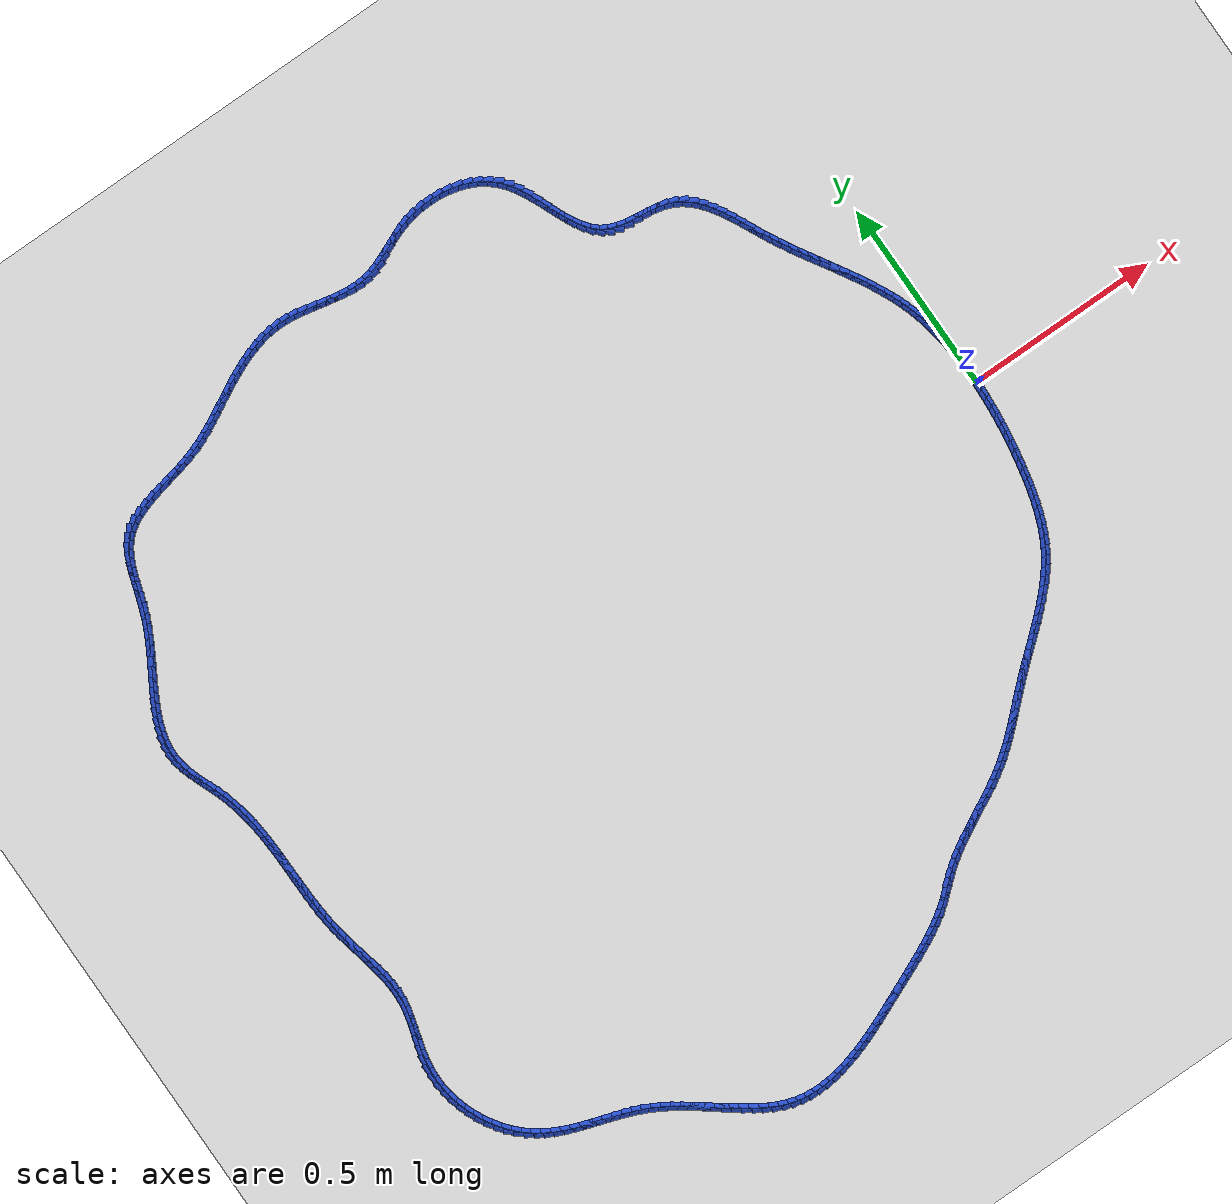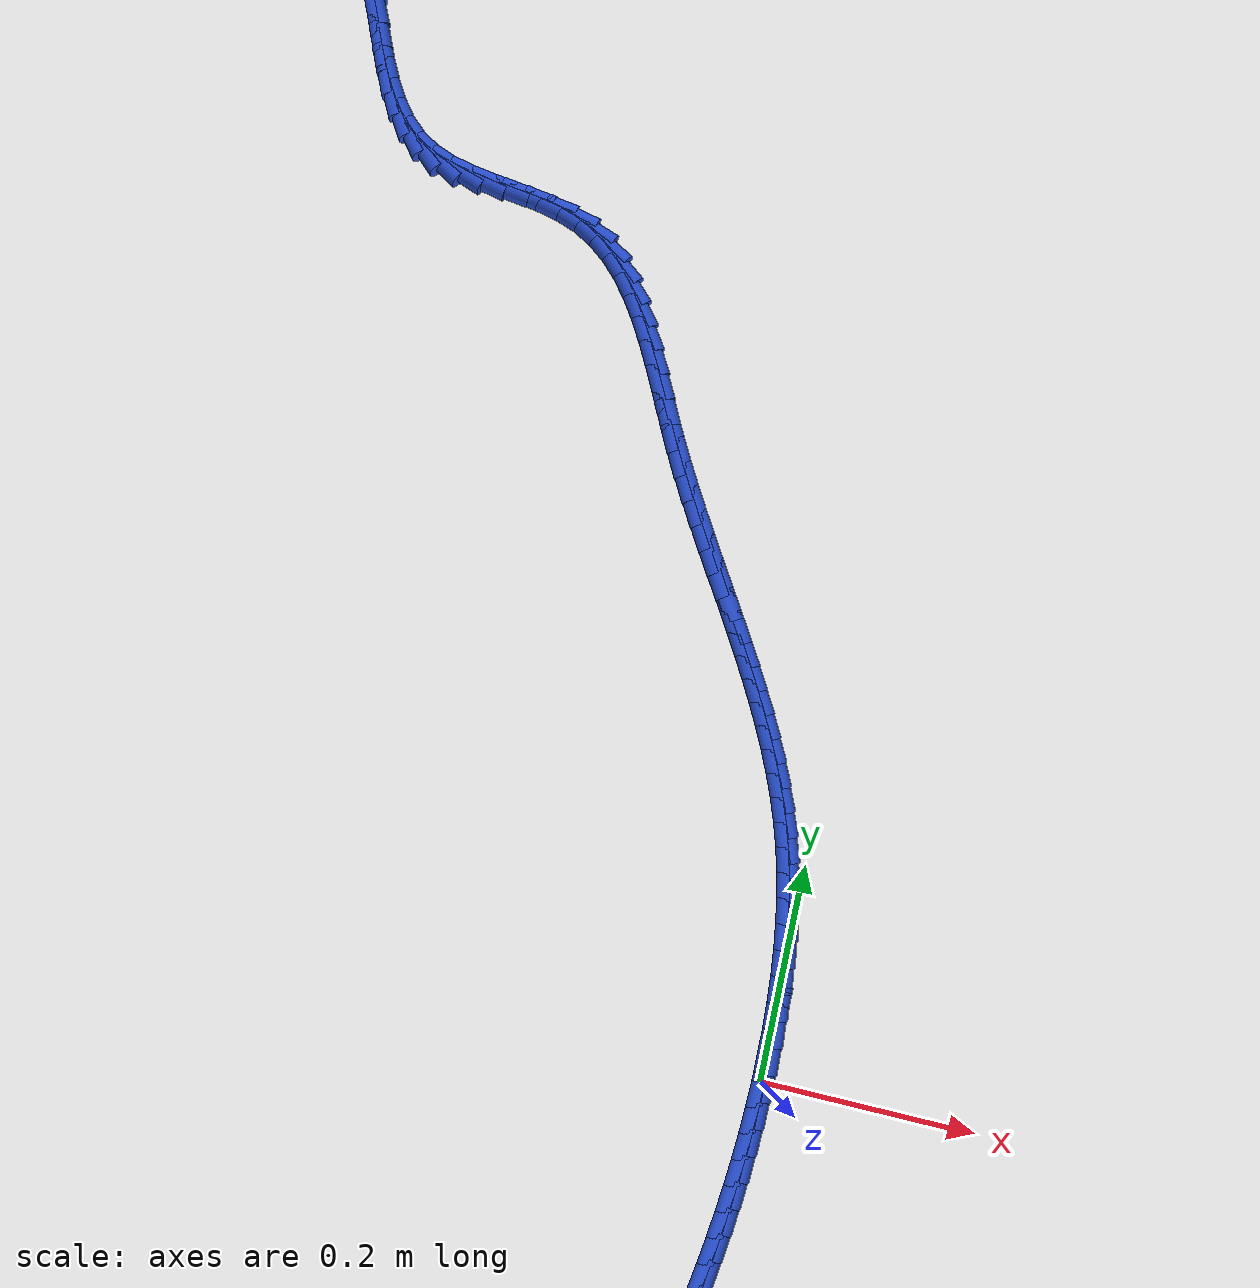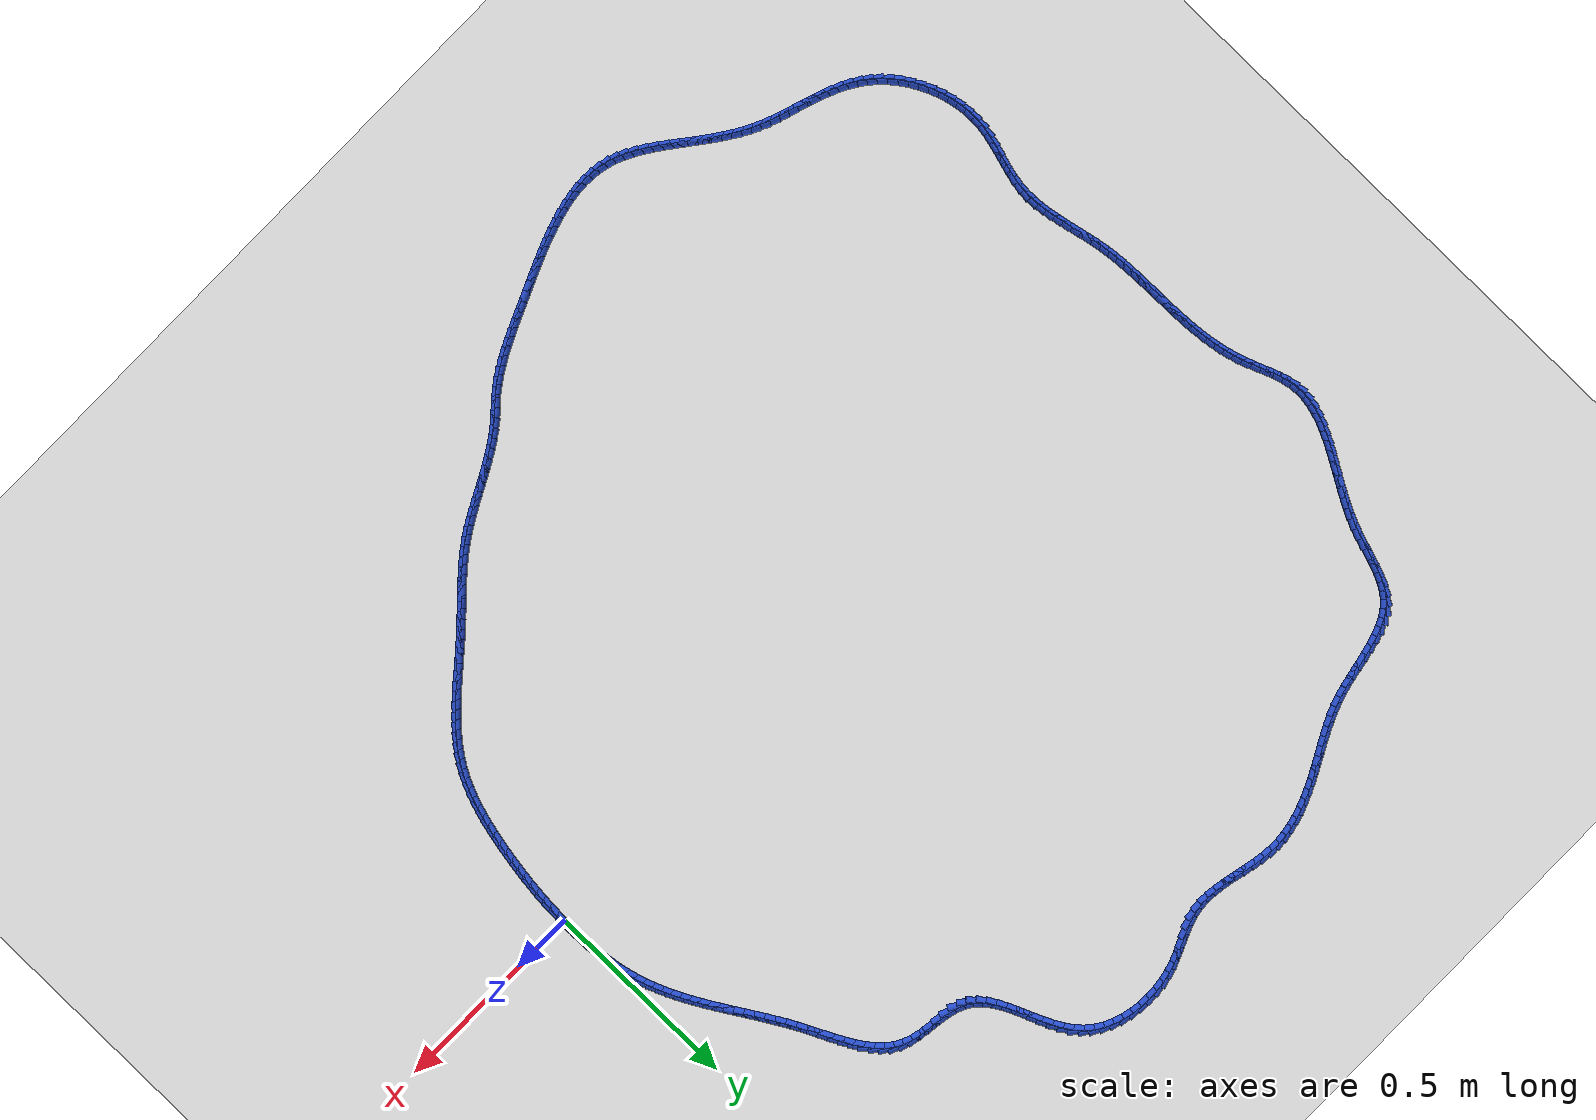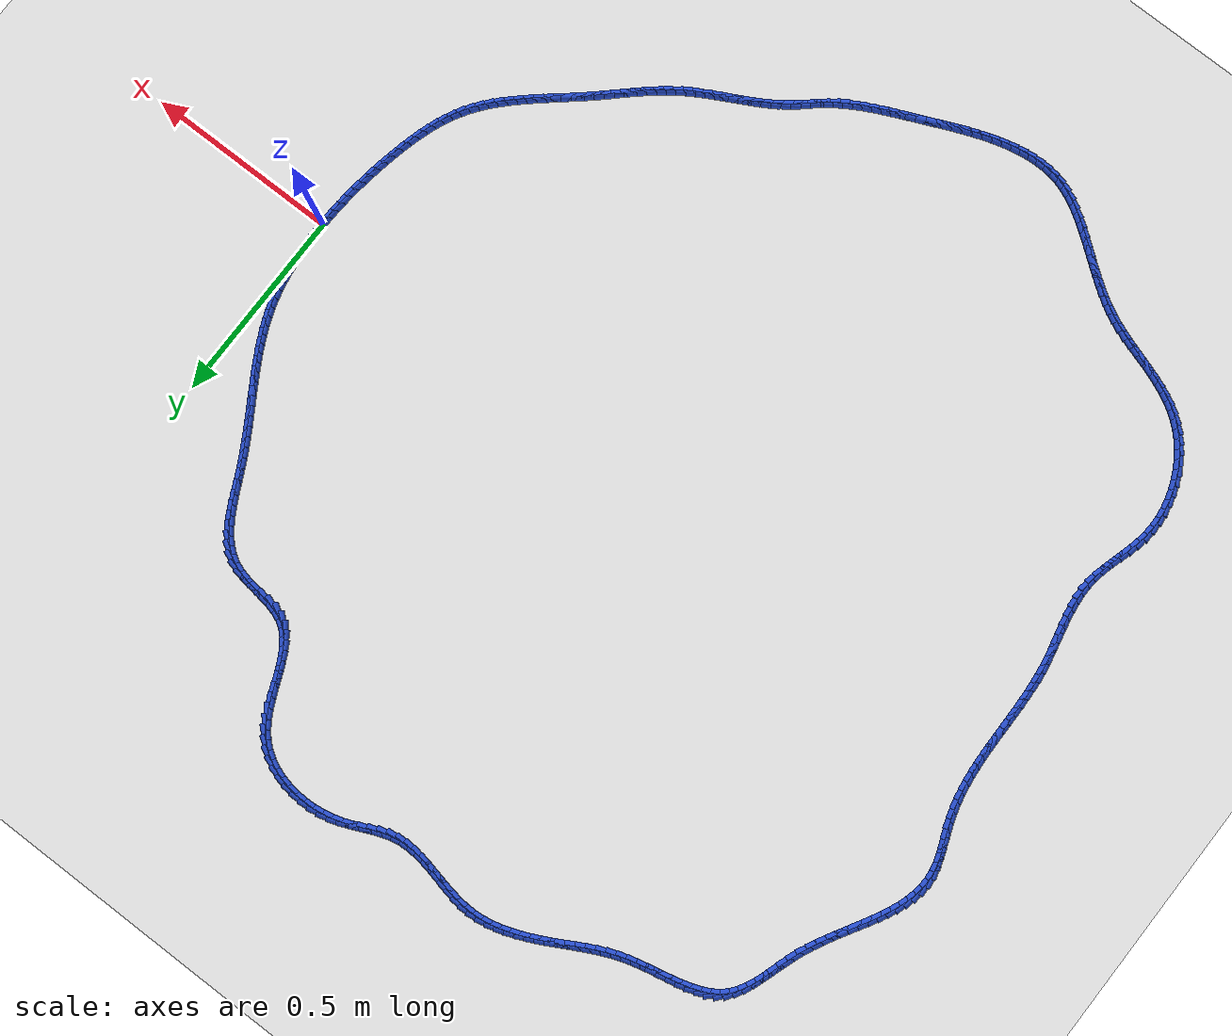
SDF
<sdf version="1.6">
 <world name="default">
  <light name="sun" type="directional">
   <pose>0 0 10 0 -0 0</pose>
   <diffuse>0.8 0.8 0.8 1</diffuse>
   <specular>0.2 0.2 0.2 1</specular>
   <attenuation>
    <range>1000</range>
    <constant>0.9</constant>
    <linear>0.01</linear>
    <quadratic>0.001</quadratic>
   </attenuation>
   <direction>-0.5 0.1 -0.9</direction>
  </light>
  <model name="ground_plane">
   <static>1</static>
   <link name="link">
    <collision name="collision">
     <geometry><plane><normal>0 0 1</normal><size>100 100</size></plane></geometry>
     <surface><friction><ode><mu>100</mu><mu2>50</mu2></ode></friction></surface>
    </collision>
    <visual name="visual">
     <cast_shadows>0</cast_shadows>
     <geometry><plane><normal>0 0 1</normal><size>100 100</size></plane></geometry>
     <material>
      <script><uri>file://media/materials/scripts/gazebo.material</uri><name>Gazebo/WhiteGlow</name></script>
     </material>
    </visual>
   </link>
  </model>
  <gravity>0 0 -9.8</gravity>
  <magnetic_field>6e-06 2.3e-05 -4.2e-05</magnetic_field>
  <atmosphere type="adiabatic"/>
  <physics name="default_physics" default="0" type="ode">
   <max_step_size>0.001</max_step_size>
   <real_time_factor>1</real_time_factor>
   <real_time_update_rate>1000</real_time_update_rate>
  </physics>
  <scene><ambient>0.4 0.4 0.4 1</ambient><background>0.7 0.7 0.7 1</background><shadows>1</shadows></scene>
  <spherical_coordinates>
   <surface_model>EARTH_WGS84</surface_model>
   <latitude_deg>0</latitude_deg>
   <longitude_deg>0</longitude_deg>
   <elevation>0</elevation>
   <heading_deg>0</heading_deg>
  </spherical_coordinates>
  <model name="line">
   <link name="link_0">
    <pose>-9.974659986866641e-18 -9.71445146547012e-17 0.01 0 1.57 1.5621484069897522</pose>
    <collision name="collision">
     <geometry><cylinder><radius>0.01</radius><length>0.08</length></cylinder></geometry>
    </collision>
    <visual name="visual">
     <material>
      <script><name>Gazebo/Blue</name><uri>file://media/materials/scripts/gazebo.material</uri></script>
     </material>
     <geometry><cylinder><radius>0.01</radius><length>0.08</length></cylinder></geometry>
    </visual>
   </link>
   <link name="link_1">
    <pose>0.00020848488752704265 0.02410749578076906 0.01 0 1.57 -1.5562668115659875</pose>
    <collision name="collision">
     <geometry><cylinder><radius>0.01</radius><length>0.08</length></cylinder></geometry>
    </collision>
    <visual name="visual">
     <material>
      <script><name>Gazebo/Blue</name><uri>file://media/materials/scripts/gazebo.material</uri></script>
     </material>
     <geometry><cylinder><radius>0.01</radius><length>0.08</length></cylinder></geometry>
    </visual>
   </link>
   <link name="link_2">
    <pose>-0.00014284811022527544 0.04828643561047386 0.01 0 1.57 -1.5308184323632508</pose>
    <collision name="collision">
     <geometry><cylinder><radius>0.01</radius><length>0.08</length></cylinder></geometry>
    </collision>
    <visual name="visual">
     <material>
      <script><name>Gazebo/Blue</name><uri>file://media/materials/scripts/gazebo.material</uri></script>
     </material>
     <geometry><cylinder><radius>0.01</radius><length>0.08</length></cylinder></geometry>
    </visual>
   </link>
   <link name="link_3">
    <pose>-0.001109999954018487 0.07246571163970908 0.01 0 1.57 -1.5029176373909436</pose>
    <collision name="collision">
     <geometry><cylinder><radius>0.01</radius><length>0.08</length></cylinder></geometry>
    </collision>
    <visual name="visual">
     <material>
      <script><name>Gazebo/Blue</name><uri>file://media/materials/scripts/gazebo.material</uri></script>
     </material>
     <geometry><cylinder><radius>0.01</radius><length>0.08</length></cylinder></geometry>
    </visual>
   </link>
   <link name="link_4">
    <pose>-0.002748971604614114 0.09657421601906961 0.01 0 1.57 -1.4723618055832173</pose>
    <collision name="collision">
     <geometry><cylinder><radius>0.01</radius><length>0.08</length></cylinder></geometry>
    </collision>
    <visual name="visual">
     <material>
      <script><name>Gazebo/Blue</name><uri>file://media/materials/scripts/gazebo.material</uri></script>
     </material>
     <geometry><cylinder><radius>0.01</radius><length>0.08</length></cylinder></geometry>
    </visual>
   </link>
   <link name="link_5">
    <pose>-0.005115764022773682 0.12054084089915029 0.01 0 1.57 -1.4389289060948756</pose>
    <collision name="collision">
     <geometry><cylinder><radius>0.01</radius><length>0.08</length></cylinder></geometry>
    </collision>
    <visual name="visual">
     <material>
      <script><name>Gazebo/Blue</name><uri>file://media/materials/scripts/gazebo.material</uri></script>
     </material>
     <geometry><cylinder><radius>0.01</radius><length>0.08</length></cylinder></geometry>
    </visual>
   </link>
   <link name="link_6">
    <pose>-0.008266378169258713 0.14429447843054588 0.01 0 1.57 -1.4023807165650055</pose>
    <collision name="collision">
     <geometry><cylinder><radius>0.01</radius><length>0.08</length></cylinder></geometry>
    </collision>
    <visual name="visual">
     <material>
      <script><name>Gazebo/Blue</name><uri>file://media/materials/scripts/gazebo.material</uri></script>
     </material>
     <geometry><cylinder><radius>0.01</radius><length>0.08</length></cylinder></geometry>
    </visual>
   </link>
   <link name="link_7">
    <pose>-0.01225681500483073 0.16776402076385136 0.01 0 1.57 -1.362468233248887</pose>
    <collision name="collision">
     <geometry><cylinder><radius>0.01</radius><length>0.08</length></cylinder></geometry>
    </collision>
    <visual name="visual">
     <material>
      <script><name>Gazebo/Blue</name><uri>file://media/materials/scripts/gazebo.material</uri></script>
     </material>
     <geometry><cylinder><radius>0.01</radius><length>0.08</length></cylinder></geometry>
    </visual>
   </link>
   <link name="link_8">
    <pose>-0.017143075490251257 0.19087836004966147 0.01 0 1.57 -1.3189401385113497</pose>
    <collision name="collision">
     <geometry><cylinder><radius>0.01</radius><length>0.08</length></cylinder></geometry>
    </collision>
    <visual name="visual">
     <material>
      <script><name>Gazebo/Blue</name><uri>file://media/materials/scripts/gazebo.material</uri></script>
     </material>
     <geometry><cylinder><radius>0.01</radius><length>0.08</length></cylinder></geometry>
    </visual>
   </link>
   <link name="link_9">
    <pose>-0.022981160586281815 0.21356638843857104 0.01 0 1.57 -1.2725637473694866</pose>
    <collision name="collision">
     <geometry><cylinder><radius>0.01</radius><length>0.08</length></cylinder></geometry>
    </collision>
    <visual name="visual">
     <material>
      <script><name>Gazebo/Blue</name><uri>file://media/materials/scripts/gazebo.material</uri></script>
     </material>
     <geometry><cylinder><radius>0.01</radius><length>0.08</length></cylinder></geometry>
    </visual>
   </link>
   <link name="link_10">
    <pose>-0.029808168838661362 0.23577520859121814 0.01 0 1.57 -1.2282336816075337</pose>
    <collision name="collision">
     <geometry><cylinder><radius>0.01</radius><length>0.08</length></cylinder></geometry>
    </collision>
    <visual name="visual">
     <material>
      <script><name>Gazebo/Blue</name><uri>file://media/materials/scripts/gazebo.material</uri></script>
     </material>
     <geometry><cylinder><radius>0.01</radius><length>0.08</length></cylinder></geometry>
    </visual>
   </link>
   <link name="link_11">
    <pose>-0.03756993506367793 0.2575398462754079 0.01 0 1.57 -1.1877903860219634</pose>
    <collision name="collision">
     <geometry><cylinder><radius>0.01</radius><length>0.08</length></cylinder></geometry>
    </collision>
    <visual name="visual">
     <material>
      <script><name>Gazebo/Blue</name><uri>file://media/materials/scripts/gazebo.material</uri></script>
     </material>
     <geometry><cylinder><radius>0.01</radius><length>0.08</length></cylinder></geometry>
    </visual>
   </link>
   <link name="link_12">
    <pose>-0.04618478674090746 0.2789218277156787 0.01 0 1.57 -1.1515464099687087</pose>
    <collision name="collision">
     <geometry><cylinder><radius>0.01</radius><length>0.08</length></cylinder></geometry>
    </collision>
    <visual name="visual">
     <material>
      <script><name>Gazebo/Blue</name><uri>file://media/materials/scripts/gazebo.material</uri></script>
     </material>
     <geometry><cylinder><radius>0.01</radius><length>0.08</length></cylinder></geometry>
    </visual>
   </link>
   <link name="link_13">
    <pose>-0.055571045725794556 0.29998268455483396 0.01 0 1.57 -1.1197120318245413</pose>
    <collision name="collision">
     <geometry><cylinder><radius>0.01</radius><length>0.08</length></cylinder></geometry>
    </collision>
    <visual name="visual">
     <material>
      <script><name>Gazebo/Blue</name><uri>file://media/materials/scripts/gazebo.material</uri></script>
     </material>
     <geometry><cylinder><radius>0.01</radius><length>0.08</length></cylinder></geometry>
    </visual>
   </link>
   <link name="link_14">
    <pose>-0.0656470338737839 0.3207839484356774 0.01 0 1.57 -1.0924095805687792</pose>
    <collision name="collision">
     <geometry><cylinder><radius>0.01</radius><length>0.08</length></cylinder></geometry>
    </collision>
    <visual name="visual">
     <material>
      <script><name>Gazebo/Blue</name><uri>file://media/materials/scripts/gazebo.material</uri></script>
     </material>
     <geometry><cylinder><radius>0.01</radius><length>0.08</length></cylinder></geometry>
    </visual>
   </link>
   <link name="link_15">
    <pose>-0.0763310730403201 0.3413871510010125 0.01 0 1.57 -1.0696900229705566</pose>
    <collision name="collision">
     <geometry><cylinder><radius>0.01</radius><length>0.08</length></cylinder></geometry>
    </collision>
    <visual name="visual">
     <material>
      <script><name>Gazebo/Blue</name><uri>file://media/materials/scripts/gazebo.material</uri></script>
     </material>
     <geometry><cylinder><radius>0.01</radius><length>0.08</length></cylinder></geometry>
    </visual>
   </link>
   <link name="link_16">
    <pose>-0.08754148508084778 0.361853823893643 0.01 0 1.57 -1.051549622548458</pose>
    <collision name="collision">
     <geometry><cylinder><radius>0.01</radius><length>0.08</length></cylinder></geometry>
    </collision>
    <visual name="visual">
     <material>
      <script><name>Gazebo/Blue</name><uri>file://media/materials/scripts/gazebo.material</uri></script>
     </material>
     <geometry><cylinder><radius>0.01</radius><length>0.08</length></cylinder></geometry>
    </visual>
   </link>
   <link name="link_17">
    <pose>-0.09919659185081163 0.3822454987563724 0.01 0 1.57 -1.0379449558422367</pose>
    <collision name="collision">
     <geometry><cylinder><radius>0.01</radius><length>0.08</length></cylinder></geometry>
    </collision>
    <visual name="visual">
     <material>
      <script><name>Gazebo/Blue</name><uri>file://media/materials/scripts/gazebo.material</uri></script>
     </material>
     <geometry><cylinder><radius>0.01</radius><length>0.08</length></cylinder></geometry>
    </visual>
   </link>
   <link name="link_18">
    <pose>-0.11121471520565619 0.40262370723200414 0.01 0 1.57 -1.0288053096682461</pose>
    <collision name="collision">
     <geometry><cylinder><radius>0.01</radius><length>0.08</length></cylinder></geometry>
    </collision>
    <visual name="visual">
     <material>
      <script><name>Gazebo/Blue</name><uri>file://media/materials/scripts/gazebo.material</uri></script>
     </material>
     <geometry><cylinder><radius>0.01</radius><length>0.08</length></cylinder></geometry>
    </visual>
   </link>
   <link name="link_19">
    <pose>-0.12351417700082622 0.4230499809633422 0.01 0 1.57 -1.0240420607333447</pose>
    <collision name="collision">
     <geometry><cylinder><radius>0.01</radius><length>0.08</length></cylinder></geometry>
    </collision>
    <visual name="visual">
     <material>
      <script><name>Gazebo/Blue</name><uri>file://media/materials/scripts/gazebo.material</uri></script>
     </material>
     <geometry><cylinder><radius>0.01</radius><length>0.08</length></cylinder></geometry>
    </visual>
   </link>
   <link name="link_20">
    <pose>-0.13601329909176632 0.44358585159318975 0.01 0 1.57 -1.0235550292447202</pose>
    <collision name="collision">
     <geometry><cylinder><radius>0.01</radius><length>0.08</length></cylinder></geometry>
    </collision>
    <visual name="visual">
     <material>
      <script><name>Gazebo/Blue</name><uri>file://media/materials/scripts/gazebo.material</uri></script>
     </material>
     <geometry><cylinder><radius>0.01</radius><length>0.08</length></cylinder></geometry>
    </visual>
   </link>
   <link name="link_21">
    <pose>-0.14863040333392114 0.4642928507643507 0.01 0 1.57 -1.0272360277824653</pose>
    <collision name="collision">
     <geometry><cylinder><radius>0.01</radius><length>0.08</length></cylinder></geometry>
    </collision>
    <visual name="visual">
     <material>
      <script><name>Gazebo/Blue</name><uri>file://media/materials/scripts/gazebo.material</uri></script>
     </material>
     <geometry><cylinder><radius>0.01</radius><length>0.08</length></cylinder></geometry>
    </visual>
   </link>
   <link name="link_22">
    <pose>-0.16128381158273522 0.4852325101196283 0.01 0 1.57 -1.0349699435198396</pose>
    <collision name="collision">
     <geometry><cylinder><radius>0.01</radius><length>0.08</length></cylinder></geometry>
    </collision>
    <visual name="visual">
     <material>
      <script><name>Gazebo/Blue</name><uri>file://media/materials/scripts/gazebo.material</uri></script>
     </material>
     <geometry><cylinder><radius>0.01</radius><length>0.08</length></cylinder></geometry>
    </visual>
   </link>
   <link name="link_23">
    <pose>-0.1738918456936533 0.5064663613018263 0.01 0 1.57 -1.0466337441758669</pose>
    <collision name="collision">
     <geometry><cylinder><radius>0.01</radius><length>0.08</length></cylinder></geometry>
    </collision>
    <visual name="visual">
     <material>
      <script><name>Gazebo/Blue</name><uri>file://media/materials/scripts/gazebo.material</uri></script>
     </material>
     <geometry><cylinder><radius>0.01</radius><length>0.08</length></cylinder></geometry>
    </visual>
   </link>
   <link name="link_24">
    <pose>-0.18637282752212 0.5280559359537487 0.01 0 1.57 -1.0620938247797163</pose>
    <collision name="collision">
     <geometry><cylinder><radius>0.01</radius><length>0.08</length></cylinder></geometry>
    </collision>
    <visual name="visual">
     <material>
      <script><name>Gazebo/Blue</name><uri>file://media/materials/scripts/gazebo.material</uri></script>
     </material>
     <geometry><cylinder><radius>0.01</radius><length>0.08</length></cylinder></geometry>
    </visual>
   </link>
   <link name="link_25">
    <pose>-0.19864507892357997 0.5500627657181983 0.01 0 1.57 -1.0812021396404852</pose>
    <collision name="collision">
     <geometry><cylinder><radius>0.01</radius><length>0.08</length></cylinder></geometry>
    </collision>
    <visual name="visual">
     <material>
      <script><name>Gazebo/Blue</name><uri>file://media/materials/scripts/gazebo.material</uri></script>
     </material>
     <geometry><cylinder><radius>0.01</radius><length>0.08</length></cylinder></geometry>
    </visual>
   </link>
   <link name="link_26">
    <pose>-0.21062692175347777 0.5725483822379792 0.01 0 1.57 -1.1025099088366677</pose>
    <collision name="collision">
     <geometry><cylinder><radius>0.01</radius><length>0.08</length></cylinder></geometry>
    </collision>
    <visual name="visual">
     <material>
      <script><name>Gazebo/Blue</name><uri>file://media/materials/scripts/gazebo.material</uri></script>
     </material>
     <geometry><cylinder><radius>0.01</radius><length>0.08</length></cylinder></geometry>
    </visual>
   </link>
   <link name="link_27">
    <pose>-0.22225908533052938 0.5955453906329737 0.01 0 1.57 -1.1139822080428494</pose>
    <collision name="collision">
     <geometry><cylinder><radius>0.01</radius><length>0.08</length></cylinder></geometry>
    </collision>
    <visual name="visual">
     <material>
      <script><name>Gazebo/Blue</name><uri>file://media/materials/scripts/gazebo.material</uri></script>
     </material>
     <geometry><cylinder><radius>0.01</radius><length>0.08</length></cylinder></geometry>
    </visual>
   </link>
   <link name="link_28">
    <pose>-0.23369452997396997 0.618812420123753 0.01 0 1.57 -1.1093493097623621</pose>
    <collision name="collision">
     <geometry><cylinder><radius>0.01</radius><length>0.08</length></cylinder></geometry>
    </collision>
    <visual name="visual">
     <material>
      <script><name>Gazebo/Blue</name><uri>file://media/materials/scripts/gazebo.material</uri></script>
     </material>
     <geometry><cylinder><radius>0.01</radius><length>0.08</length></cylinder></geometry>
    </visual>
   </link>
   <link name="link_29">
    <pose>-0.24520323994148469 0.6419570299236813 0.01 0 1.57 -1.0882714877261002</pose>
    <collision name="collision">
     <geometry><cylinder><radius>0.01</radius><length>0.08</length></cylinder></geometry>
    </collision>
    <visual name="visual">
     <material>
      <script><name>Gazebo/Blue</name><uri>file://media/materials/scripts/gazebo.material</uri></script>
     </material>
     <geometry><cylinder><radius>0.01</radius><length>0.08</length></cylinder></geometry>
    </visual>
   </link>
   <link name="link_30">
    <pose>-0.2570564234254391 0.6645851992290472 0.01 0 1.57 -1.0496134372135149</pose>
    <collision name="collision">
     <geometry><cylinder><radius>0.01</radius><length>0.08</length></cylinder></geometry>
    </collision>
    <visual name="visual">
     <material>
      <script><name>Gazebo/Blue</name><uri>file://media/materials/scripts/gazebo.material</uri></script>
     </material>
     <geometry><cylinder><radius>0.01</radius><length>0.08</length></cylinder></geometry>
    </visual>
   </link>
   <link name="link_31">
    <pose>-0.26952528861819897 0.6863029072361392 0.01 0 1.57 -0.9914254164824424</pose>
    <collision name="collision">
     <geometry><cylinder><radius>0.01</radius><length>0.08</length></cylinder></geometry>
    </collision>
    <visual name="visual">
     <material>
      <script><name>Gazebo/Blue</name><uri>file://media/materials/scripts/gazebo.material</uri></script>
     </material>
     <geometry><cylinder><radius>0.01</radius><length>0.08</length></cylinder></geometry>
    </visual>
   </link>
   <link name="link_32">
    <pose>-0.28288104371213013 0.7067161331412463 0.01 0 1.57 -0.9111544199915123</pose>
    <collision name="collision">
     <geometry><cylinder><radius>0.01</radius><length>0.08</length></cylinder></geometry>
    </collision>
    <visual name="visual">
     <material>
      <script><name>Gazebo/Blue</name><uri>file://media/materials/scripts/gazebo.material</uri></script>
     </material>
     <geometry><cylinder><radius>0.01</radius><length>0.08</length></cylinder></geometry>
    </visual>
   </link>
   <link name="link_33">
    <pose>-0.2973948968995982 0.7254308561406568 0.01 0 1.57 -0.8062467416112244</pose>
    <collision name="collision">
     <geometry><cylinder><radius>0.01</radius><length>0.08</length></cylinder></geometry>
    </collision>
    <visual name="visual">
     <material>
      <script><name>Gazebo/Blue</name><uri>file://media/materials/scripts/gazebo.material</uri></script>
     </material>
     <geometry><cylinder><radius>0.01</radius><length>0.08</length></cylinder></geometry>
    </visual>
   </link>
   <link name="link_34">
    <pose>-0.31333805637296885 0.7420530554306594 0.01 0 1.57 -0.6754564530873327</pose>
    <collision name="collision">
     <geometry><cylinder><radius>0.01</radius><length>0.08</length></cylinder></geometry>
    </collision>
    <visual name="visual">
     <material>
      <script><name>Gazebo/Blue</name><uri>file://media/materials/scripts/gazebo.material</uri></script>
     </material>
     <geometry><cylinder><radius>0.01</radius><length>0.08</length></cylinder></geometry>
    </visual>
   </link>
   <link name="link_35">
    <pose>-0.33098173032460776 0.7561887102075426 0.01 0 1.57 -0.5209233462219436</pose>
    <collision name="collision">
     <geometry><cylinder><radius>0.01</radius><length>0.08</length></cylinder></geometry>
    </collision>
    <visual name="visual">
     <material>
      <script><name>Gazebo/Blue</name><uri>file://media/materials/scripts/gazebo.material</uri></script>
     </material>
     <geometry><cylinder><radius>0.01</radius><length>0.08</length></cylinder></geometry>
    </visual>
   </link>
   <link name="link_36">
    <pose>-0.35059712694688094 0.7674437996675956 0.01 0 1.57 -0.35553507025811215</pose>
    <collision name="collision">
     <geometry><cylinder><radius>0.01</radius><length>0.08</length></cylinder></geometry>
    </collision>
    <visual name="visual">
     <material>
      <script><name>Gazebo/Blue</name><uri>file://media/materials/scripts/gazebo.material</uri></script>
     </material>
     <geometry><cylinder><radius>0.01</radius><length>0.08</length></cylinder></geometry>
    </visual>
   </link>
   <link name="link_37">
    <pose>-0.3723788104568487 0.7755316405064875 0.01 0 1.57 -0.23048972635414242</pose>
    <collision name="collision">
     <geometry><cylinder><radius>0.01</radius><length>0.08</length></cylinder></geometry>
    </collision>
    <visual name="visual">
     <material>
      <script><name>Gazebo/Blue</name><uri>file://media/materials/scripts/gazebo.material</uri></script>
     </material>
     <geometry><cylinder><radius>0.01</radius><length>0.08</length></cylinder></geometry>
    </visual>
   </link>
   <link name="link_38">
    <pose>-0.3958905824394532 0.7810489128331942 0.01 0 1.57 -0.16097174557308125</pose>
    <collision name="collision">
     <geometry><cylinder><radius>0.01</radius><length>0.08</length></cylinder></geometry>
    </collision>
    <visual name="visual">
     <material>
      <script><name>Gazebo/Blue</name><uri>file://media/materials/scripts/gazebo.material</uri></script>
     </material>
     <geometry><cylinder><radius>0.01</radius><length>0.08</length></cylinder></geometry>
    </visual>
   </link>
   <link name="link_39">
    <pose>-0.42038624782034467 0.7850264374193119 0.01 0 1.57 -0.13946243954434678</pose>
    <collision name="collision">
     <geometry><cylinder><radius>0.01</radius><length>0.08</length></cylinder></geometry>
    </collision>
    <visual name="visual">
     <material>
      <script><name>Gazebo/Blue</name><uri>file://media/materials/scripts/gazebo.material</uri></script>
     </material>
     <geometry><cylinder><radius>0.01</radius><length>0.08</length></cylinder></geometry>
    </visual>
   </link>
   <link name="link_40">
    <pose>-0.4451174593423917 0.7884980491013664 0.01 0 1.57 -0.16366713858289234</pose>
    <collision name="collision">
     <geometry><cylinder><radius>0.01</radius><length>0.08</length></cylinder></geometry>
    </collision>
    <visual name="visual">
     <material>
      <script><name>Gazebo/Blue</name><uri>file://media/materials/scripts/gazebo.material</uri></script>
     </material>
     <geometry><cylinder><radius>0.01</radius><length>0.08</length></cylinder></geometry>
    </visual>
   </link>
   <link name="link_41">
    <pose>-0.4693358697484632 0.7924975827158844 0.01 0 1.57 -0.23766697471989442</pose>
    <collision name="collision">
     <geometry><cylinder><radius>0.01</radius><length>0.08</length></cylinder></geometry>
    </collision>
    <visual name="visual">
     <material>
      <script><name>Gazebo/Blue</name><uri>file://media/materials/scripts/gazebo.material</uri></script>
     </material>
     <geometry><cylinder><radius>0.01</radius><length>0.08</length></cylinder></geometry>
    </visual>
   </link>
   <link name="link_42">
    <pose>-0.49229313178142764 0.7980588730993914 0.01 0 1.57 -0.37132779115681885</pose>
    <collision name="collision">
     <geometry><cylinder><radius>0.01</radius><length>0.08</length></cylinder></geometry>
    </collision>
    <visual name="visual">
     <material>
      <script><name>Gazebo/Blue</name><uri>file://media/materials/scripts/gazebo.material</uri></script>
     </material>
     <geometry><cylinder><radius>0.01</radius><length>0.08</length></cylinder></geometry>
    </visual>
   </link>
   <link name="link_43">
    <pose>-0.5132408981841533 0.8062157550884133 0.01 0 1.57 -0.5666934449704307</pose>
    <collision name="collision">
     <geometry><cylinder><radius>0.01</radius><length>0.08</length></cylinder></geometry>
    </collision>
    <visual name="visual">
     <material>
      <script><name>Gazebo/Blue</name><uri>file://media/materials/scripts/gazebo.material</uri></script>
     </material>
     <geometry><cylinder><radius>0.01</radius><length>0.08</length></cylinder></geometry>
    </visual>
   </link>
   <link name="link_44">
    <pose>-0.5315393916927527 0.817859331315224 0.01 0 1.57 -0.7605467806046483</pose>
    <collision name="collision">
     <geometry><cylinder><radius>0.01</radius><length>0.08</length></cylinder></geometry>
    </collision>
    <visual name="visual">
     <material>
      <script><name>Gazebo/Blue</name><uri>file://media/materials/scripts/gazebo.material</uri></script>
     </material>
     <geometry><cylinder><radius>0.01</radius><length>0.08</length></cylinder></geometry>
    </visual>
   </link>
   <link name="link_45">
    <pose>-0.5473166561955773 0.8328712836480607 0.01 0 1.57 -0.9150220830545429</pose>
    <collision name="collision">
     <geometry><cylinder><radius>0.01</radius><length>0.08</length></cylinder></geometry>
    </collision>
    <visual name="visual">
     <material>
      <script><name>Gazebo/Blue</name><uri>file://media/materials/scripts/gazebo.material</uri></script>
     </material>
     <geometry><cylinder><radius>0.01</radius><length>0.08</length></cylinder></geometry>
    </visual>
   </link>
   <link name="link_46">
    <pose>-0.5610317952950661 0.8506980642814812 0.01 0 1.57 -1.0281246258088235</pose>
    <collision name="collision">
     <geometry><cylinder><radius>0.01</radius><length>0.08</length></cylinder></geometry>
    </collision>
    <visual name="visual">
     <material>
      <script><name>Gazebo/Blue</name><uri>file://media/materials/scripts/gazebo.material</uri></script>
     </material>
     <geometry><cylinder><radius>0.01</radius><length>0.08</length></cylinder></geometry>
    </visual>
   </link>
   <link name="link_47">
    <pose>-0.573145213518439 0.8707844151413385 0.01 0 1.57 -1.1043342231362312</pose>
    <collision name="collision">
     <geometry><cylinder><radius>0.01</radius><length>0.08</length></cylinder></geometry>
    </collision>
    <visual name="visual">
     <material>
      <script><name>Gazebo/Blue</name><uri>file://media/materials/scripts/gazebo.material</uri></script>
     </material>
     <geometry><cylinder><radius>0.01</radius><length>0.08</length></cylinder></geometry>
    </visual>
   </link>
   <link name="link_48">
    <pose>-0.5841173153929161 0.8925750781534855 0.01 0 1.57 -1.1490915395457144</pose>
    <collision name="collision">
     <geometry><cylinder><radius>0.01</radius><length>0.08</length></cylinder></geometry>
    </collision>
    <visual name="visual">
     <material>
      <script><name>Gazebo/Blue</name><uri>file://media/materials/scripts/gazebo.material</uri></script>
     </material>
     <geometry><cylinder><radius>0.01</radius><length>0.08</length></cylinder></geometry>
    </visual>
   </link>
   <link name="link_49">
    <pose>-0.5944085054457175 0.9155147952437757 0.01 0 1.57 -1.1664470477522946</pose>
    <collision name="collision">
     <geometry><cylinder><radius>0.01</radius><length>0.08</length></cylinder></geometry>
    </collision>
    <visual name="visual">
     <material>
      <script><name>Gazebo/Blue</name><uri>file://media/materials/scripts/gazebo.material</uri></script>
     </material>
     <geometry><cylinder><radius>0.01</radius><length>0.08</length></cylinder></geometry>
    </visual>
   </link>
   <link name="link_50">
    <pose>-0.6044791882040634 0.939048308338062 0.01 0 1.57 -1.1584639515517923</pose>
    <collision name="collision">
     <geometry><cylinder><radius>0.01</radius><length>0.08</length></cylinder></geometry>
    </collision>
    <visual name="visual">
     <material>
      <script><name>Gazebo/Blue</name><uri>file://media/materials/scripts/gazebo.material</uri></script>
     </material>
     <geometry><cylinder><radius>0.01</radius><length>0.08</length></cylinder></geometry>
    </visual>
   </link>
   <link name="link_51">
    <pose>-0.6147897681951736 0.9626203593621977 0.01 0 1.57 -1.1252409215385817</pose>
    <collision name="collision">
     <geometry><cylinder><radius>0.01</radius><length>0.08</length></cylinder></geometry>
    </collision>
    <visual name="visual">
     <material>
      <script><name>Gazebo/Blue</name><uri>file://media/materials/scripts/gazebo.material</uri></script>
     </material>
     <geometry><cylinder><radius>0.01</radius><length>0.08</length></cylinder></geometry>
    </visual>
   </link>
   <link name="link_52">
    <pose>-0.6258006499462685 0.9856756902420363 0.01 0 1.57 -1.0651375557721678</pose>
    <collision name="collision">
     <geometry><cylinder><radius>0.01</radius><length>0.08</length></cylinder></geometry>
    </collision>
    <visual name="visual">
     <material>
      <script><name>Gazebo/Blue</name><uri>file://media/materials/scripts/gazebo.material</uri></script>
     </material>
     <geometry><cylinder><radius>0.01</radius><length>0.08</length></cylinder></geometry>
    </visual>
   </link>
   <link name="link_53">
    <pose>-0.6379722379845679 1.007659042903431 0.01 0 1.57 -0.9752830277168776</pose>
    <collision name="collision">
     <geometry><cylinder><radius>0.01</radius><length>0.08</length></cylinder></geometry>
    </collision>
    <visual name="visual">
     <material>
      <script><name>Gazebo/Blue</name><uri>file://media/materials/scripts/gazebo.material</uri></script>
     </material>
     <geometry><cylinder><radius>0.01</radius><length>0.08</length></cylinder></geometry>
    </visual>
   </link>
   <link name="link_54">
    <pose>-0.651764936837292 1.0280151592722342 0.01 0 1.57 -0.8528761698114475</pose>
    <collision name="collision">
     <geometry><cylinder><radius>0.01</radius><length>0.08</length></cylinder></geometry>
    </collision>
    <visual name="visual">
     <material>
      <script><name>Gazebo/Blue</name><uri>file://media/materials/scripts/gazebo.material</uri></script>
     </material>
     <geometry><cylinder><radius>0.01</radius><length>0.08</length></cylinder></geometry>
    </visual>
   </link>
   <link name="link_55">
    <pose>-0.6676382767135091 1.0461894593850107 0.01 0 1.57 -0.7089371878396424</pose>
    <collision name="collision">
     <geometry><cylinder><radius>0.01</radius><length>0.08</length></cylinder></geometry>
    </collision>
    <visual name="visual">
     <material>
      <script><name>Gazebo/Blue</name><uri>file://media/materials/scripts/gazebo.material</uri></script>
     </material>
     <geometry><cylinder><radius>0.01</radius><length>0.08</length></cylinder></geometry>
    </visual>
   </link>
   <link name="link_56">
    <pose>-0.6858344083324771 1.061795960213074 0.01 0 1.57 -0.5719670868590997</pose>
    <collision name="collision">
     <geometry><cylinder><radius>0.01</radius><length>0.08</length></cylinder></geometry>
    </collision>
    <visual name="visual">
     <material>
      <script><name>Gazebo/Blue</name><uri>file://media/materials/scripts/gazebo.material</uri></script>
     </material>
     <geometry><cylinder><radius>0.01</radius><length>0.08</length></cylinder></geometry>
    </visual>
   </link>
   <link name="link_57">
    <pose>-0.7060937215211623 1.0748378384800723 0.01 0 1.57 -0.4467381063991091</pose>
    <collision name="collision">
     <geometry><cylinder><radius>0.01</radius><length>0.08</length></cylinder></geometry>
    </collision>
    <visual name="visual">
     <material>
      <script><name>Gazebo/Blue</name><uri>file://media/materials/scripts/gazebo.material</uri></script>
     </material>
     <geometry><cylinder><radius>0.01</radius><length>0.08</length></cylinder></geometry>
    </visual>
   </link>
   <link name="link_58">
    <pose>-0.7280860389759922 1.0853730019328667 0.01 0 1.57 -0.33278760443191946</pose>
    <collision name="collision">
     <geometry><cylinder><radius>0.01</radius><length>0.08</length></cylinder></geometry>
    </collision>
    <visual name="visual">
     <material>
      <script><name>Gazebo/Blue</name><uri>file://media/materials/scripts/gazebo.material</uri></script>
     </material>
     <geometry><cylinder><radius>0.01</radius><length>0.08</length></cylinder></geometry>
    </visual>
   </link>
   <link name="link_59">
    <pose>-0.751481183393395 1.0934593583183192 0.01 0 1.57 -0.22870105658260492</pose>
    <collision name="collision">
     <geometry><cylinder><radius>0.01</radius><length>0.08</length></cylinder></geometry>
    </collision>
    <visual name="visual">
     <material>
      <script><name>Gazebo/Blue</name><uri>file://media/materials/scripts/gazebo.material</uri></script>
     </material>
     <geometry><cylinder><radius>0.01</radius><length>0.08</length></cylinder></geometry>
    </visual>
   </link>
   <link name="link_60">
    <pose>-0.7759489774697987 1.0991548153832906 0.01 0 1.57 -0.1325942717282767</pose>
    <collision name="collision">
     <geometry><cylinder><radius>0.01</radius><length>0.08</length></cylinder></geometry>
    </collision>
    <visual name="visual">
     <material>
      <script><name>Gazebo/Blue</name><uri>file://media/materials/scripts/gazebo.material</uri></script>
     </material>
     <geometry><cylinder><radius>0.01</radius><length>0.08</length></cylinder></geometry>
    </visual>
   </link>
   <link name="link_61">
    <pose>-0.801159243901631 1.102517280874642 0.01 0 1.57 -0.04241299491118357</pose>
    <collision name="collision">
     <geometry><cylinder><radius>0.01</radius><length>0.08</length></cylinder></geometry>
    </collision>
    <visual name="visual">
     <material>
      <script><name>Gazebo/Blue</name><uri>file://media/materials/scripts/gazebo.material</uri></script>
     </material>
     <geometry><cylinder><radius>0.01</radius><length>0.08</length></cylinder></geometry>
    </visual>
   </link>
   <link name="link_62">
    <pose>-0.8267818053853201 1.1036046625392355 0.01 0 1.57 0.0439245988772277</pose>
    <collision name="collision">
     <geometry><cylinder><radius>0.01</radius><length>0.08</length></cylinder></geometry>
    </collision>
    <visual name="visual">
     <material>
      <script><name>Gazebo/Blue</name><uri>file://media/materials/scripts/gazebo.material</uri></script>
     </material>
     <geometry><cylinder><radius>0.01</radius><length>0.08</length></cylinder></geometry>
    </visual>
   </link>
   <link name="link_63">
    <pose>-0.8524864846172938 1.1024748681239318 0.01 0 1.57 0.12849082655115898</pose>
    <collision name="collision">
     <geometry><cylinder><radius>0.01</radius><length>0.08</length></cylinder></geometry>
    </collision>
    <visual name="visual">
     <material>
      <script><name>Gazebo/Blue</name><uri>file://media/materials/scripts/gazebo.material</uri></script>
     </material>
     <geometry><cylinder><radius>0.01</radius><length>0.08</length></cylinder></geometry>
    </visual>
   </link>
   <link name="link_64">
    <pose>-0.8779431042939801 1.099185805375592 0.01 0 1.57 0.21337275242029086</pose>
    <collision name="collision">
     <geometry><cylinder><radius>0.01</radius><length>0.08</length></cylinder></geometry>
    </collision>
    <visual name="visual">
     <material>
      <script><name>Gazebo/Blue</name><uri>file://media/materials/scripts/gazebo.material</uri></script>
     </material>
     <geometry><cylinder><radius>0.01</radius><length>0.08</length></cylinder></geometry>
    </visual>
   </link>
   <link name="link_65">
    <pose>-0.9028214871118068 1.093795382041078 0.01 0 1.57 0.2996032688060958</pose>
    <collision name="collision">
     <geometry><cylinder><radius>0.01</radius><length>0.08</length></cylinder></geometry>
    </collision>
    <visual name="visual">
     <material>
      <script><name>Gazebo/Blue</name><uri>file://media/materials/scripts/gazebo.material</uri></script>
     </material>
     <geometry><cylinder><radius>0.01</radius><length>0.08</length></cylinder></geometry>
    </visual>
   </link>
   <link name="link_66">
    <pose>-0.9268093896995869 1.0863854803362365 0.01 0 1.57 0.369549002037685</pose>
    <collision name="collision">
     <geometry><cylinder><radius>0.01</radius><length>0.08</length></cylinder></geometry>
    </collision>
    <visual name="visual">
     <material>
      <script><name>Gazebo/Blue</name><uri>file://media/materials/scripts/gazebo.material</uri></script>
     </material>
     <geometry><cylinder><radius>0.01</radius><length>0.08</length></cylinder></geometry>
    </visual>
   </link>
   <link name="link_67">
    <pose>-0.949897199752444 1.077442546236705 0.01 0 1.57 0.4063975860002821</pose>
    <collision name="collision">
     <geometry><cylinder><radius>0.01</radius><length>0.08</length></cylinder></geometry>
    </collision>
    <visual name="visual">
     <material>
      <script><name>Gazebo/Blue</name><uri>file://media/materials/scripts/gazebo.material</uri></script>
     </material>
     <geometry><cylinder><radius>0.01</radius><length>0.08</length></cylinder></geometry>
    </visual>
   </link>
   <link name="link_68">
    <pose>-0.9723271547373453 1.0677897039443227 0.01 0 1.57 0.40839170961009696</pose>
    <collision name="collision">
     <geometry><cylinder><radius>0.01</radius><length>0.08</length></cylinder></geometry>
    </collision>
    <visual name="visual">
     <material>
      <script><name>Gazebo/Blue</name><uri>file://media/materials/scripts/gazebo.material</uri></script>
     </material>
     <geometry><cylinder><radius>0.01</radius><length>0.08</length></cylinder></geometry>
    </visual>
   </link>
   <link name="link_69">
    <pose>-0.9943491622572667 1.0582603312647634 0.01 0 1.57 0.37366419731571077</pose>
    <collision name="collision">
     <geometry><cylinder><radius>0.01</radius><length>0.08</length></cylinder></geometry>
    </collision>
    <visual name="visual">
     <material>
      <script><name>Gazebo/Blue</name><uri>file://media/materials/scripts/gazebo.material</uri></script>
     </material>
     <geometry><cylinder><radius>0.01</radius><length>0.08</length></cylinder></geometry>
    </visual>
   </link>
   <link name="link_70">
    <pose>-1.0162131299151849 1.0496878060037012 0.01 0 1.57 0.29960772419895326</pose>
    <collision name="collision">
     <geometry><cylinder><radius>0.01</radius><length>0.08</length></cylinder></geometry>
    </collision>
    <visual name="visual">
     <material>
      <script><name>Gazebo/Blue</name><uri>file://media/materials/scripts/gazebo.material</uri></script>
     </material>
     <geometry><cylinder><radius>0.01</radius><length>0.08</length></cylinder></geometry>
    </visual>
   </link>
   <link name="link_71">
    <pose>-1.038168965314077 1.0429055059668109 0.01 0 1.57 0.18490531621057138</pose>
    <collision name="collision">
     <geometry><cylinder><radius>0.01</radius><length>0.08</length></cylinder></geometry>
    </collision>
    <visual name="visual">
     <material>
      <script><name>Gazebo/Blue</name><uri>file://media/materials/scripts/gazebo.material</uri></script>
     </material>
     <geometry><cylinder><radius>0.01</radius><length>0.08</length></cylinder></geometry>
    </visual>
   </link>
   <link name="link_72">
    <pose>-1.06046396266168 1.0387354085762412 0.01 0 1.57 0.05624951157760972</pose>
    <collision name="collision">
     <geometry><cylinder><radius>0.01</radius><length>0.08</length></cylinder></geometry>
    </collision>
    <visual name="visual">
     <material>
      <script><name>Gazebo/Blue</name><uri>file://media/materials/scripts/gazebo.material</uri></script>
     </material>
     <geometry><cylinder><radius>0.01</radius><length>0.08</length></cylinder></geometry>
    </visual>
   </link>
   <link name="link_73">
    <pose>-1.0832203736721846 1.0374540198452828 0.01 0 1.57 -0.04786980906195709</pose>
    <collision name="collision">
     <geometry><cylinder><radius>0.01</radius><length>0.08</length></cylinder></geometry>
    </collision>
    <visual name="visual">
     <material>
      <script><name>Gazebo/Blue</name><uri>file://media/materials/scripts/gazebo.material</uri></script>
     </material>
     <geometry><cylinder><radius>0.01</radius><length>0.08</length></cylinder></geometry>
    </visual>
   </link>
   <link name="link_74">
    <pose>-1.1063829769597664 1.0385636569562495 0.01 0 1.57 -0.12462992173371414</pose>
    <collision name="collision">
     <geometry><cylinder><radius>0.01</radius><length>0.08</length></cylinder></geometry>
    </collision>
    <visual name="visual">
     <material>
      <script><name>Gazebo/Blue</name><uri>file://media/materials/scripts/gazebo.material</uri></script>
     </material>
     <geometry><cylinder><radius>0.01</radius><length>0.08</length></cylinder></geometry>
    </visual>
   </link>
   <link name="link_75">
    <pose>-1.1298830468937548 1.041507727681919 0.01 0 1.57 -0.17579058910191128</pose>
    <collision name="collision">
     <geometry><cylinder><radius>0.01</radius><length>0.08</length></cylinder></geometry>
    </collision>
    <visual name="visual">
     <material>
      <script><name>Gazebo/Blue</name><uri>file://media/materials/scripts/gazebo.material</uri></script>
     </material>
     <geometry><cylinder><radius>0.01</radius><length>0.08</length></cylinder></geometry>
    </visual>
   </link>
   <link name="link_76">
    <pose>-1.1536518578434793 1.0457296397950673 0.01 0 1.57 -0.20338151477144173</pose>
    <collision name="collision">
     <geometry><cylinder><radius>0.01</radius><length>0.08</length></cylinder></geometry>
    </collision>
    <visual name="visual">
     <material>
      <script><name>Gazebo/Blue</name><uri>file://media/materials/scripts/gazebo.material</uri></script>
     </material>
     <geometry><cylinder><radius>0.01</radius><length>0.08</length></cylinder></geometry>
    </visual>
   </link>
   <link name="link_77">
    <pose>-1.1776206841782693 1.0506728010684716 0.01 0 1.57 -0.20885109954804257</pose>
    <collision name="collision">
     <geometry><cylinder><radius>0.01</radius><length>0.08</length></cylinder></geometry>
    </collision>
    <visual name="visual">
     <material>
      <script><name>Gazebo/Blue</name><uri>file://media/materials/scripts/gazebo.material</uri></script>
     </material>
     <geometry><cylinder><radius>0.01</radius><length>0.08</length></cylinder></geometry>
    </visual>
   </link>
   <link name="link_78">
    <pose>-1.2017208002674544 1.0557806192749093 0.01 0 1.57 -0.19274914241024937</pose>
    <collision name="collision">
     <geometry><cylinder><radius>0.01</radius><length>0.08</length></cylinder></geometry>
    </collision>
    <visual name="visual">
     <material>
      <script><name>Gazebo/Blue</name><uri>file://media/materials/scripts/gazebo.material</uri></script>
     </material>
     <geometry><cylinder><radius>0.01</radius><length>0.08</length></cylinder></geometry>
    </visual>
   </link>
   <link name="link_79">
    <pose>-1.2258834804803633 1.0604965021871566 0.01 0 1.57 -0.1547097906782739</pose>
    <collision name="collision">
     <geometry><cylinder><radius>0.01</radius><length>0.08</length></cylinder></geometry>
    </collision>
    <visual name="visual">
     <material>
      <script><name>Gazebo/Blue</name><uri>file://media/materials/scripts/gazebo.material</uri></script>
     </material>
     <geometry><cylinder><radius>0.01</radius><length>0.08</length></cylinder></geometry>
    </visual>
   </link>
   <link name="link_80">
    <pose>-1.2500399991863256 1.0642638575779906 0.01 0 1.57 -0.09366541770067531</pose>
    <collision name="collision">
     <geometry><cylinder><radius>0.01</radius><length>0.08</length></cylinder></geometry>
    </collision>
    <visual name="visual">
     <material>
      <script><name>Gazebo/Blue</name><uri>file://media/materials/scripts/gazebo.material</uri></script>
     </material>
     <geometry><cylinder><radius>0.01</radius><length>0.08</length></cylinder></geometry>
    </visual>
   </link>
   <link name="link_81">
    <pose>-1.2741216307546708 1.066526093220188 0.01 0 1.57 -0.008721796539898302</pose>
    <collision name="collision">
     <geometry><cylinder><radius>0.01</radius><length>0.08</length></cylinder></geometry>
    </collision>
    <visual name="visual">
     <material>
      <script><name>Gazebo/Blue</name><uri>file://media/materials/scripts/gazebo.material</uri></script>
     </material>
     <geometry><cylinder><radius>0.01</radius><length>0.08</length></cylinder></geometry>
    </visual>
   </link>
   <link name="link_82">
    <pose>-1.2980600378528797 1.0667348844306455 0.01 0 1.57 0.08647618509906822</pose>
    <collision name="collision">
     <geometry><cylinder><radius>0.01</radius><length>0.08</length></cylinder></geometry>
    </collision>
    <visual name="visual">
     <material>
      <script><name>Gazebo/Blue</name><uri>file://media/materials/scripts/gazebo.material</uri></script>
     </material>
     <geometry><cylinder><radius>0.01</radius><length>0.08</length></cylinder></geometry>
    </visual>
   </link>
   <link name="link_83">
    <pose>-1.3218026018359992 1.064676584768645 0.01 0 1.57 0.17247524556729593</pose>
    <collision name="collision">
     <geometry><cylinder><radius>0.01</radius><length>0.08</length></cylinder></geometry>
    </collision>
    <visual name="visual">
     <material>
      <script><name>Gazebo/Blue</name><uri>file://media/materials/scripts/gazebo.material</uri></script>
     </material>
     <geometry><cylinder><radius>0.01</radius><length>0.08</length></cylinder></geometry>
    </visual>
   </link>
   <link name="link_84">
    <pose>-1.3453174914587496 1.060580147747044 0.01 0 1.57 0.2474472027159994</pose>
    <collision name="collision">
     <geometry><cylinder><radius>0.01</radius><length>0.08</length></cylinder></geometry>
    </collision>
    <visual name="visual">
     <material>
      <script><name>Gazebo/Blue</name><uri>file://media/materials/scripts/gazebo.material</uri></script>
     </material>
     <geometry><cylinder><radius>0.01</radius><length>0.08</length></cylinder></geometry>
    </visual>
   </link>
   <link name="link_85">
    <pose>-1.3685743024062427 1.054704908712613 0.01 0 1.57 0.3114728816057139</pose>
    <collision name="collision">
     <geometry><cylinder><radius>0.01</radius><length>0.08</length></cylinder></geometry>
    </collision>
    <visual name="visual">
     <material>
      <script><name>Gazebo/Blue</name><uri>file://media/materials/scripts/gazebo.material</uri></script>
     </material>
     <geometry><cylinder><radius>0.01</radius><length>0.08</length></cylinder></geometry>
    </visual>
   </link>
   <link name="link_86">
    <pose>-1.3915426303635903 1.047310203012124 0.01 0 1.57 0.3649994658263487</pose>
    <collision name="collision">
     <geometry><cylinder><radius>0.01</radius><length>0.08</length></cylinder></geometry>
    </collision>
    <visual name="visual">
     <material>
      <script><name>Gazebo/Blue</name><uri>file://media/materials/scripts/gazebo.material</uri></script>
     </material>
     <geometry><cylinder><radius>0.01</radius><length>0.08</length></cylinder></geometry>
    </visual>
   </link>
   <link name="link_87">
    <pose>-1.4141920710159026 1.038655365992347 0.01 0 1.57 0.4086146388637475</pose>
    <collision name="collision">
     <geometry><cylinder><radius>0.01</radius><length>0.08</length></cylinder></geometry>
    </collision>
    <visual name="visual">
     <material>
      <script><name>Gazebo/Blue</name><uri>file://media/materials/scripts/gazebo.material</uri></script>
     </material>
     <geometry><cylinder><radius>0.01</radius><length>0.08</length></cylinder></geometry>
    </visual>
   </link>
   <link name="link_88">
    <pose>-1.4364922200482915 1.028999733000054 0.01 0 1.57 0.44288533850997686</pose>
    <collision name="collision">
     <geometry><cylinder><radius>0.01</radius><length>0.08</length></cylinder></geometry>
    </collision>
    <visual name="visual">
     <material>
      <script><name>Gazebo/Blue</name><uri>file://media/materials/scripts/gazebo.material</uri></script>
     </material>
     <geometry><cylinder><radius>0.01</radius><length>0.08</length></cylinder></geometry>
    </visual>
   </link>
   <link name="link_89">
    <pose>-1.4584126731458673 1.018602639382016 0.01 0 1.57 0.46824573908860495</pose>
    <collision name="collision">
     <geometry><cylinder><radius>0.01</radius><length>0.08</length></cylinder></geometry>
    </collision>
    <visual name="visual">
     <material>
      <script><name>Gazebo/Blue</name><uri>file://media/materials/scripts/gazebo.material</uri></script>
     </material>
     <geometry><cylinder><radius>0.01</radius><length>0.08</length></cylinder></geometry>
    </visual>
   </link>
   <link name="link_90">
    <pose>-1.479923650835961 1.0077232269129632 0.01 0 1.57 0.4843762856761829</pose>
    <collision name="collision">
     <geometry><cylinder><radius>0.01</radius><length>0.08</length></cylinder></geometry>
    </collision>
    <visual name="visual">
     <material>
      <script><name>Gazebo/Blue</name><uri>file://media/materials/scripts/gazebo.material</uri></script>
     </material>
     <geometry><cylinder><radius>0.01</radius><length>0.08</length></cylinder></geometry>
    </visual>
   </link>
   <link name="link_91">
    <pose>-1.5010644336563144 0.9965992430272708 0.01 0 1.57 0.49006831949686797</pose>
    <collision name="collision">
     <geometry><cylinder><radius>0.01</radius><length>0.08</length></cylinder></geometry>
    </collision>
    <visual name="visual">
     <material>
      <script><name>Gazebo/Blue</name><uri>file://media/materials/scripts/gazebo.material</uri></script>
     </material>
     <geometry><cylinder><radius>0.01</radius><length>0.08</length></cylinder></geometry>
    </visual>
   </link>
   <link name="link_92">
    <pose>-1.522005042913264 0.9854279325227596 0.01 0 1.57 0.48495443753367795</pose>
    <collision name="collision">
     <geometry><cylinder><radius>0.01</radius><length>0.08</length></cylinder></geometry>
    </collision>
    <visual name="visual">
     <material>
      <script><name>Gazebo/Blue</name><uri>file://media/materials/scripts/gazebo.material</uri></script>
     </material>
     <geometry><cylinder><radius>0.01</radius><length>0.08</length></cylinder></geometry>
    </visual>
   </link>
   <link name="link_93">
    <pose>-1.5429300594402802 0.9744020297508015 0.01 0 1.57 0.46897167493604397</pose>
    <collision name="collision">
     <geometry><cylinder><radius>0.01</radius><length>0.08</length></cylinder></geometry>
    </collision>
    <visual name="visual">
     <material>
      <script><name>Gazebo/Blue</name><uri>file://media/materials/scripts/gazebo.material</uri></script>
     </material>
     <geometry><cylinder><radius>0.01</radius><length>0.08</length></cylinder></geometry>
    </visual>
   </link>
   <link name="link_94">
    <pose>-1.5640240640708292 0.9637142690627678 0.01 0 1.57 0.4422792945330084</pose>
    <collision name="collision">
     <geometry><cylinder><radius>0.01</radius><length>0.08</length></cylinder></geometry>
    </collision>
    <visual name="visual">
     <material>
      <script><name>Gazebo/Blue</name><uri>file://media/materials/scripts/gazebo.material</uri></script>
     </material>
     <geometry><cylinder><radius>0.01</radius><length>0.08</length></cylinder></geometry>
    </visual>
   </link>
   <link name="link_95">
    <pose>-1.585471637638378 0.9535573848100296 0.01 0 1.57 0.4053075068800579</pose>
    <collision name="collision">
     <geometry><cylinder><radius>0.01</radius><length>0.08</length></cylinder></geometry>
    </collision>
    <visual name="visual">
     <material>
      <script><name>Gazebo/Blue</name><uri>file://media/materials/scripts/gazebo.material</uri></script>
     </material>
     <geometry><cylinder><radius>0.01</radius><length>0.08</length></cylinder></geometry>
    </visual>
   </link>
   <link name="link_96">
    <pose>-1.6074573609763947 0.9441241113439587 0.01 0 1.57 0.3588192412352773</pose>
    <collision name="collision">
     <geometry><cylinder><radius>0.01</radius><length>0.08</length></cylinder></geometry>
    </collision>
    <visual name="visual">
     <material>
      <script><name>Gazebo/Blue</name><uri>file://media/materials/scripts/gazebo.material</uri></script>
     </material>
     <geometry><cylinder><radius>0.01</radius><length>0.08</length></cylinder></geometry>
    </visual>
   </link>
   <link name="link_97">
    <pose>-1.6301658149183462 0.9356071830159265 0.01 0 1.57 0.3043173310538755</pose>
    <collision name="collision">
     <geometry><cylinder><radius>0.01</radius><length>0.08</length></cylinder></geometry>
    </collision>
    <visual name="visual">
     <material>
      <script><name>Gazebo/Blue</name><uri>file://media/materials/scripts/gazebo.material</uri></script>
     </material>
     <geometry><cylinder><radius>0.01</radius><length>0.08</length></cylinder></geometry>
    </visual>
   </link>
   <link name="link_98">
    <pose>-1.6537748708994935 0.9281922146343788 0.01 0 1.57 0.25507290129477644</pose>
    <collision name="collision">
     <geometry><cylinder><radius>0.01</radius><length>0.08</length></cylinder></geometry>
    </collision>
    <visual name="visual">
     <material>
      <script><name>Gazebo/Blue</name><uri>file://media/materials/scripts/gazebo.material</uri></script>
     </material>
     <geometry><cylinder><radius>0.01</radius><length>0.08</length></cylinder></geometry>
    </visual>
   </link>
   <link name="link_99">
    <pose>-1.67822792825987 0.9218160156610782 0.01 0 1.57 0.22492422806569026</pose>
    <collision name="collision">
     <geometry><cylinder><radius>0.01</radius><length>0.08</length></cylinder></geometry>
    </collision>
    <visual name="visual">
     <material>
      <script><name>Gazebo/Blue</name><uri>file://media/materials/scripts/gazebo.material</uri></script>
     </material>
     <geometry><cylinder><radius>0.01</radius><length>0.08</length></cylinder></geometry>
    </visual>
   </link>
   <link name="link_100">
    <pose>-1.703178225076942 0.9161074967715482 0.01 0 1.57 0.21323288389922973</pose>
    <collision name="collision">
     <geometry><cylinder><radius>0.01</radius><length>0.08</length></cylinder></geometry>
    </collision>
    <visual name="visual">
     <material>
      <script><name>Gazebo/Blue</name><uri>file://media/materials/scripts/gazebo.material</uri></script>
     </material>
     <geometry><cylinder><radius>0.01</radius><length>0.08</length></cylinder></geometry>
    </visual>
   </link>
   <link name="link_101">
    <pose>-1.7282609934033621 0.9106764619103341 0.01 0 1.57 0.21949018105076332</pose>
    <collision name="collision">
     <geometry><cylinder><radius>0.01</radius><length>0.08</length></cylinder></geometry>
    </collision>
    <visual name="visual">
     <material>
      <script><name>Gazebo/Blue</name><uri>file://media/materials/scripts/gazebo.material</uri></script>
     </material>
     <geometry><cylinder><radius>0.01</radius><length>0.08</length></cylinder></geometry>
    </visual>
   </link>
   <link name="link_102">
    <pose>-1.7531114652917867 0.905132715021981 0.01 0 1.57 0.24433061902375822</pose>
    <collision name="collision">
     <geometry><cylinder><radius>0.01</radius><length>0.08</length></cylinder></geometry>
    </collision>
    <visual name="visual">
     <material>
      <script><name>Gazebo/Blue</name><uri>file://media/materials/scripts/gazebo.material</uri></script>
     </material>
     <geometry><cylinder><radius>0.01</radius><length>0.08</length></cylinder></geometry>
    </visual>
   </link>
   <link name="link_103">
    <pose>-1.7773648727948703 0.8990860600510344 0.01 0 1.57 0.28957635305568613</pose>
    <collision name="collision">
     <geometry><cylinder><radius>0.01</radius><length>0.08</length></cylinder></geometry>
    </collision>
    <visual name="visual">
     <material>
      <script><name>Gazebo/Blue</name><uri>file://media/materials/scripts/gazebo.material</uri></script>
     </material>
     <geometry><cylinder><radius>0.01</radius><length>0.08</length></cylinder></geometry>
    </visual>
   </link>
   <link name="link_104">
    <pose>-1.8006564479652671 0.8921463009420394 0.01 0 1.57 0.358219491051253</pose>
    <collision name="collision">
     <geometry><cylinder><radius>0.01</radius><length>0.08</length></cylinder></geometry>
    </collision>
    <visual name="visual">
     <material>
      <script><name>Gazebo/Blue</name><uri>file://media/materials/scripts/gazebo.material</uri></script>
     </material>
     <geometry><cylinder><radius>0.01</radius><length>0.08</length></cylinder></geometry>
    </visual>
   </link>
   <link name="link_105">
    <pose>-1.8226214228556312 0.883923241639541 0.01 0 1.57 0.454122527125674</pose>
    <collision name="collision">
     <geometry><cylinder><radius>0.01</radius><length>0.08</length></cylinder></geometry>
    </collision>
    <visual name="visual">
     <material>
      <script><name>Gazebo/Blue</name><uri>file://media/materials/scripts/gazebo.material</uri></script>
     </material>
     <geometry><cylinder><radius>0.01</radius><length>0.08</length></cylinder></geometry>
    </visual>
   </link>
   <link name="link_106">
    <pose>-1.8428950295186173 0.874026686088084 0.01 0 1.57 0.5809494316735487</pose>
    <collision name="collision">
     <geometry><cylinder><radius>0.01</radius><length>0.08</length></cylinder></geometry>
    </collision>
    <visual name="visual">
     <material>
      <script><name>Gazebo/Blue</name><uri>file://media/materials/scripts/gazebo.material</uri></script>
     </material>
     <geometry><cylinder><radius>0.01</radius><length>0.08</length></cylinder></geometry>
    </visual>
   </link>
   <link name="link_107">
    <pose>-1.8611125000068802 0.8620664382322144 0.01 0 1.57 0.7395971888846131</pose>
    <collision name="collision">
     <geometry><cylinder><radius>0.01</radius><length>0.08</length></cylinder></geometry>
    </collision>
    <visual name="visual">
     <material>
      <script><name>Gazebo/Blue</name><uri>file://media/materials/scripts/gazebo.material</uri></script>
     </material>
     <geometry><cylinder><radius>0.01</radius><length>0.08</length></cylinder></geometry>
    </visual>
   </link>
   <link name="link_108">
    <pose>-1.8769102276098624 0.8476533631759922 0.01 0 1.57 0.9090441128880818</pose>
    <collision name="collision">
     <geometry><cylinder><radius>0.01</radius><length>0.08</length></cylinder></geometry>
    </collision>
    <visual name="visual">
     <material>
      <script><name>Gazebo/Blue</name><uri>file://media/materials/scripts/gazebo.material</uri></script>
     </material>
     <geometry><cylinder><radius>0.01</radius><length>0.08</length></cylinder></geometry>
    </visual>
   </link>
   <link name="link_109">
    <pose>-1.890173382354377 0.8306256627773887 0.01 0 1.57 1.0460444347230606</pose>
    <collision name="collision">
     <geometry><cylinder><radius>0.01</radius><length>0.08</length></cylinder></geometry>
    </collision>
    <visual name="visual">
     <material>
      <script><name>Gazebo/Blue</name><uri>file://media/materials/scripts/gazebo.material</uri></script>
     </material>
     <geometry><cylinder><radius>0.01</radius><length>0.08</length></cylinder></geometry>
    </visual>
   </link>
   <link name="link_110">
    <pose>-1.901343467620338 0.8113299265351325 0.01 0 1.57 1.144907023624097</pose>
    <collision name="collision">
     <geometry><cylinder><radius>0.01</radius><length>0.08</length></cylinder></geometry>
    </collision>
    <visual name="visual">
     <material>
      <script><name>Gazebo/Blue</name><uri>file://media/materials/scripts/gazebo.material</uri></script>
     </material>
     <geometry><cylinder><radius>0.01</radius><length>0.08</length></cylinder></geometry>
    </visual>
   </link>
   <link name="link_111">
    <pose>-1.9109374610502545 0.79018171371596 0.01 0 1.57 1.2094872235053047</pose>
    <collision name="collision">
     <geometry><cylinder><radius>0.01</radius><length>0.08</length></cylinder></geometry>
    </collision>
    <visual name="visual">
     <material>
      <script><name>Gazebo/Blue</name><uri>file://media/materials/scripts/gazebo.material</uri></script>
     </material>
     <geometry><cylinder><radius>0.01</radius><length>0.08</length></cylinder></geometry>
    </visual>
   </link>
   <link name="link_112">
    <pose>-1.9194723402866363 0.7675965835866083 0.01 0 1.57 1.2443290268625944</pose>
    <collision name="collision">
     <geometry><cylinder><radius>0.01</radius><length>0.08</length></cylinder></geometry>
    </collision>
    <visual name="visual">
     <material>
      <script><name>Gazebo/Blue</name><uri>file://media/materials/scripts/gazebo.material</uri></script>
     </material>
     <geometry><cylinder><radius>0.01</radius><length>0.08</length></cylinder></geometry>
    </visual>
   </link>
   <link name="link_113">
    <pose>-1.927465082971992 0.7439900954138136 0.01 0 1.57 1.2528859340526544</pose>
    <collision name="collision">
     <geometry><cylinder><radius>0.01</radius><length>0.08</length></cylinder></geometry>
    </collision>
    <visual name="visual">
     <material>
      <script><name>Gazebo/Blue</name><uri>file://media/materials/scripts/gazebo.material</uri></script>
     </material>
     <geometry><cylinder><radius>0.01</radius><length>0.08</length></cylinder></geometry>
    </visual>
   </link>
   <link name="link_114">
    <pose>-1.935432666748831 0.7197778084643126 0.01 0 1.57 1.2370992716952982</pose>
    <collision name="collision">
     <geometry><cylinder><radius>0.01</radius><length>0.08</length></cylinder></geometry>
    </collision>
    <visual name="visual">
     <material>
      <script><name>Gazebo/Blue</name><uri>file://media/materials/scripts/gazebo.material</uri></script>
     </material>
     <geometry><cylinder><radius>0.01</radius><length>0.08</length></cylinder></geometry>
    </visual>
   </link>
   <link name="link_115">
    <pose>-1.9438920692596633 0.6953752820048421 0.01 0 1.57 1.1977263452398683</pose>
    <collision name="collision">
     <geometry><cylinder><radius>0.01</radius><length>0.08</length></cylinder></geometry>
    </collision>
    <visual name="visual">
     <material>
      <script><name>Gazebo/Blue</name><uri>file://media/materials/scripts/gazebo.material</uri></script>
     </material>
     <geometry><cylinder><radius>0.01</radius><length>0.08</length></cylinder></geometry>
    </visual>
   </link>
   <link name="link_116">
    <pose>-1.9533559763289021 0.6711956032524032 0.01 0 1.57 1.1472152273104441</pose>
    <collision name="collision">
     <geometry><cylinder><radius>0.01</radius><length>0.08</length></cylinder></geometry>
    </collision>
    <visual name="visual">
     <material>
      <script><name>Gazebo/Blue</name><uri>file://media/materials/scripts/gazebo.material</uri></script>
     </material>
     <geometry><cylinder><radius>0.01</radius><length>0.08</length></cylinder></geometry>
    </visual>
   </link>
   <link name="link_117">
    <pose>-1.9640466722915622 0.6474845907026369 0.01 0 1.57 1.1059123445928145</pose>
    <collision name="collision">
     <geometry><cylinder><radius>0.01</radius><length>0.08</length></cylinder></geometry>
    </collision>
    <visual name="visual">
     <material>
      <script><name>Gazebo/Blue</name><uri>file://media/materials/scripts/gazebo.material</uri></script>
     </material>
     <geometry><cylinder><radius>0.01</radius><length>0.08</length></cylinder></geometry>
    </visual>
   </link>
   <link name="link_118">
    <pose>-1.9757163124480934 0.6242172726336521 0.01 0 1.57 1.0754501926508044</pose>
    <collision name="collision">
     <geometry><cylinder><radius>0.01</radius><length>0.08</length></cylinder></geometry>
    </collision>
    <visual name="visual">
     <material>
      <script><name>Gazebo/Blue</name><uri>file://media/materials/scripts/gazebo.material</uri></script>
     </material>
     <geometry><cylinder><radius>0.01</radius><length>0.08</length></cylinder></geometry>
    </visual>
   </link>
   <link name="link_119">
    <pose>-1.9880741786594904 0.6013439825969147 0.01 0 1.57 1.0556176077382937</pose>
    <collision name="collision">
     <geometry><cylinder><radius>0.01</radius><length>0.08</length></cylinder></geometry>
    </collision>
    <visual name="visual">
     <material>
      <script><name>Gazebo/Blue</name><uri>file://media/materials/scripts/gazebo.material</uri></script>
     </material>
     <geometry><cylinder><radius>0.01</radius><length>0.08</length></cylinder></geometry>
    </visual>
   </link>
   <link name="link_120">
    <pose>-2.0008295527867492 0.57881505414389 0.01 0 1.57 1.0463471422072523</pose>
    <collision name="collision">
     <geometry><cylinder><radius>0.01</radius><length>0.08</length></cylinder></geometry>
    </collision>
    <visual name="visual">
     <material>
      <script><name>Gazebo/Blue</name><uri>file://media/materials/scripts/gazebo.material</uri></script>
     </material>
     <geometry><cylinder><radius>0.01</radius><length>0.08</length></cylinder></geometry>
    </visual>
   </link>
   <link name="link_121">
    <pose>-2.0136917166908654 0.556580820826044 0.01 0 1.57 1.0477856871473894</pose>
    <collision name="collision">
     <geometry><cylinder><radius>0.01</radius><length>0.08</length></cylinder></geometry>
    </collision>
    <visual name="visual">
     <material>
      <script><name>Gazebo/Blue</name><uri>file://media/materials/scripts/gazebo.material</uri></script>
     </material>
     <geometry><cylinder><radius>0.01</radius><length>0.08</length></cylinder></geometry>
    </visual>
   </link>
   <link name="link_122">
    <pose>-2.0263699522328356 0.5345916161948421 0.01 0 1.57 1.060341632944363</pose>
    <collision name="collision">
     <geometry><cylinder><radius>0.01</radius><length>0.08</length></cylinder></geometry>
    </collision>
    <visual name="visual">
     <material>
      <script><name>Gazebo/Blue</name><uri>file://media/materials/scripts/gazebo.material</uri></script>
     </material>
     <geometry><cylinder><radius>0.01</radius><length>0.08</length></cylinder></geometry>
    </visual>
   </link>
   <link name="link_123">
    <pose>-2.0385735412736548 0.51279777380175 0.01 0 1.57 1.0847113944787083</pose>
    <collision name="collision">
     <geometry><cylinder><radius>0.01</radius><length>0.08</length></cylinder></geometry>
    </collision>
    <visual name="visual">
     <material>
      <script><name>Gazebo/Blue</name><uri>file://media/materials/scripts/gazebo.material</uri></script>
     </material>
     <geometry><cylinder><radius>0.01</radius><length>0.08</length></cylinder></geometry>
    </visual>
   </link>
   <link name="link_124">
    <pose>-2.0500117656743178 0.49114962719823324 0.01 0 1.57 1.1218772731203674</pose>
    <collision name="collision">
     <geometry><cylinder><radius>0.01</radius><length>0.08</length></cylinder></geometry>
    </collision>
    <visual name="visual">
     <material>
      <script><name>Gazebo/Blue</name><uri>file://media/materials/scripts/gazebo.material</uri></script>
     </material>
     <geometry><cylinder><radius>0.01</radius><length>0.08</length></cylinder></geometry>
    </visual>
   </link>
   <link name="link_125">
    <pose>-2.0603939072958224 0.46959750993575716 0.01 0 1.57 1.1730527700990665</pose>
    <collision name="collision">
     <geometry><cylinder><radius>0.01</radius><length>0.08</length></cylinder></geometry>
    </collision>
    <visual name="visual">
     <material>
      <script><name>Gazebo/Blue</name><uri>file://media/materials/scripts/gazebo.material</uri></script>
     </material>
     <geometry><cylinder><radius>0.01</radius><length>0.08</length></cylinder></geometry>
    </visual>
   </link>
   <link name="link_126">
    <pose>-2.0694292479991634 0.44809175556578773 0.01 0 1.57 1.23953049397752</pose>
    <collision name="collision">
     <geometry><cylinder><radius>0.01</radius><length>0.08</length></cylinder></geometry>
    </collision>
    <visual name="visual">
     <material>
      <script><name>Gazebo/Blue</name><uri>file://media/materials/scripts/gazebo.material</uri></script>
     </material>
     <geometry><cylinder><radius>0.01</radius><length>0.08</length></cylinder></geometry>
    </visual>
   </link>
   <link name="link_127">
    <pose>-2.0768270696453355 0.4265826976397902 0.01 0 1.57 1.3223689440794009</pose>
    <collision name="collision">
     <geometry><cylinder><radius>0.01</radius><length>0.08</length></cylinder></geometry>
    </collision>
    <visual name="visual">
     <material>
      <script><name>Gazebo/Blue</name><uri>file://media/materials/scripts/gazebo.material</uri></script>
     </material>
     <geometry><cylinder><radius>0.01</radius><length>0.08</length></cylinder></geometry>
    </visual>
   </link>
   <link name="link_128">
    <pose>-2.082296654095336 0.40502066970923034 0.01 0 1.57 1.4218644215103293</pose>
    <collision name="collision">
     <geometry><cylinder><radius>0.01</radius><length>0.08</length></cylinder></geometry>
    </collision>
    <visual name="visual">
     <material>
      <script><name>Gazebo/Blue</name><uri>file://media/materials/scripts/gazebo.material</uri></script>
     </material>
     <geometry><cylinder><radius>0.01</radius><length>0.08</length></cylinder></geometry>
    </visual>
   </link>
   <link name="link_129">
    <pose>-2.08554728321016 0.3833560053255738 0.01 0 1.57 1.5368470182176228</pose>
    <collision name="collision">
     <geometry><cylinder><radius>0.01</radius><length>0.08</length></cylinder></geometry>
    </collision>
    <visual name="visual">
     <material>
      <script><name>Gazebo/Blue</name><uri>file://media/materials/scripts/gazebo.material</uri></script>
     </material>
     <geometry><cylinder><radius>0.01</radius><length>0.08</length></cylinder></geometry>
    </visual>
   </link>
   <link name="link_130">
    <pose>-2.086288238850803 0.3615390380402861 0.01 0 1.57 -1.477563913934521</pose>
    <collision name="collision">
     <geometry><cylinder><radius>0.01</radius><length>0.08</length></cylinder></geometry>
    </collision>
    <visual name="visual">
     <material>
      <script><name>Gazebo/Blue</name><uri>file://media/materials/scripts/gazebo.material</uri></script>
     </material>
     <geometry><cylinder><radius>0.01</radius><length>0.08</length></cylinder></geometry>
    </visual>
   </link>
   <link name="link_131">
    <pose>-2.0842293950761372 0.3395201403071636 0.01 0 1.57 -1.355084771426268</pose>
    <collision name="collision">
     <geometry><cylinder><radius>0.01</radius><length>0.08</length></cylinder></geometry>
    </collision>
    <visual name="visual">
     <material>
      <script><name>Gazebo/Blue</name><uri>file://media/materials/scripts/gazebo.material</uri></script>
     </material>
     <geometry><cylinder><radius>0.01</radius><length>0.08</length></cylinder></geometry>
    </visual>
   </link>
   <link name="link_132">
    <pose>-2.079353401047162 0.3172676035690075 0.01 0 1.57 -1.2685861178584672</pose>
    <collision name="collision">
     <geometry><cylinder><radius>0.01</radius><length>0.08</length></cylinder></geometry>
    </collision>
    <visual name="visual">
     <material>
      <script><name>Gazebo/Blue</name><uri>file://media/materials/scripts/gazebo.material</uri></script>
     </material>
     <geometry><cylinder><radius>0.01</radius><length>0.08</length></cylinder></geometry>
    </visual>
   </link>
   <link name="link_133">
    <pose>-2.072347667654535 0.2947960160808528 0.01 0 1.57 -1.2184218512035216</pose>
    <collision name="collision">
     <geometry><cylinder><radius>0.01</radius><length>0.08</length></cylinder></geometry>
    </collision>
    <visual name="visual">
     <material>
      <script><name>Gazebo/Blue</name><uri>file://media/materials/scripts/gazebo.material</uri></script>
     </material>
     <geometry><cylinder><radius>0.01</radius><length>0.08</length></cylinder></geometry>
    </visual>
   </link>
   <link name="link_134">
    <pose>-2.064011904746796 0.27212734317788395 0.01 0 1.57 -1.200575009292439</pose>
    <collision name="collision">
     <geometry><cylinder><radius>0.01</radius><length>0.08</length></cylinder></geometry>
    </collision>
    <visual name="visual">
     <material>
      <script><name>Gazebo/Blue</name><uri>file://media/materials/scripts/gazebo.material</uri></script>
     </material>
     <geometry><cylinder><radius>0.01</radius><length>0.08</length></cylinder></geometry>
    </visual>
   </link>
   <link name="link_135">
    <pose>-2.0551458221724865 0.24928355019528642 0.01 0 1.57 -1.2130615933202187</pose>
    <collision name="collision">
     <geometry><cylinder><radius>0.01</radius><length>0.08</length></cylinder></geometry>
    </collision>
    <visual name="visual">
     <material>
      <script><name>Gazebo/Blue</name><uri>file://media/materials/scripts/gazebo.material</uri></script>
     </material>
     <geometry><cylinder><radius>0.01</radius><length>0.08</length></cylinder></geometry>
    </visual>
   </link>
   <link name="link_136">
    <pose>-2.0465491297801464 0.22628660246824575 0.01 0 1.57 -1.2549384913884487</pose>
    <collision name="collision">
     <geometry><cylinder><radius>0.01</radius><length>0.08</length></cylinder></geometry>
    </collision>
    <visual name="visual">
     <material>
      <script><name>Gazebo/Blue</name><uri>file://media/materials/scripts/gazebo.material</uri></script>
     </material>
     <geometry><cylinder><radius>0.01</radius><length>0.08</length></cylinder></geometry>
    </visual>
   </link>
   <link name="link_137">
    <pose>-2.03899074133949 0.2031580217587222 0.01 0 1.57 -1.3083483973395047</pose>
    <collision name="collision">
     <geometry><cylinder><radius>0.01</radius><length>0.08</length></cylinder></geometry>
    </collision>
    <visual name="visual">
     <material>
      <script><name>Gazebo/Blue</name><uri>file://media/materials/scripts/gazebo.material</uri></script>
     </material>
     <geometry><cylinder><radius>0.01</radius><length>0.08</length></cylinder></geometry>
    </visual>
   </link>
   <link name="link_138">
    <pose>-2.0327458861857797 0.17991221901440765 0.01 0 1.57 -1.3576903473757294</pose>
    <collision name="collision">
     <geometry><cylinder><radius>0.01</radius><length>0.08</length></cylinder></geometry>
    </collision>
    <visual name="visual">
     <material>
      <script><name>Gazebo/Blue</name><uri>file://media/materials/scripts/gazebo.material</uri></script>
     </material>
     <geometry><cylinder><radius>0.01</radius><length>0.08</length></cylinder></geometry>
    </visual>
   </link>
   <link name="link_139">
    <pose>-2.027692200981264 0.15655787843235175 0.01 0 1.57 -1.4020360274577137</pose>
    <collision name="collision">
     <geometry><cylinder><radius>0.01</radius><length>0.08</length></cylinder></geometry>
    </collision>
    <visual name="visual">
     <material>
      <script><name>Gazebo/Blue</name><uri>file://media/materials/scripts/gazebo.material</uri></script>
     </material>
     <geometry><cylinder><radius>0.01</radius><length>0.08</length></cylinder></geometry>
    </visual>
   </link>
   <link name="link_140">
    <pose>-2.023696027403088 0.13310352152158808 0.01 0 1.57 -1.4410469260590248</pose>
    <collision name="collision">
     <geometry><cylinder><radius>0.01</radius><length>0.08</length></cylinder></geometry>
    </collision>
    <visual name="visual">
     <material>
      <script><name>Gazebo/Blue</name><uri>file://media/materials/scripts/gazebo.material</uri></script>
     </material>
     <geometry><cylinder><radius>0.01</radius><length>0.08</length></cylinder></geometry>
    </visual>
   </link>
   <link name="link_141">
    <pose>-2.020623707128395 0.10955766979114916 0.01 0 1.57 -1.474512709069848</pose>
    <collision name="collision">
     <geometry><cylinder><radius>0.01</radius><length>0.08</length></cylinder></geometry>
    </collision>
    <visual name="visual">
     <material>
      <script><name>Gazebo/Blue</name><uri>file://media/materials/scripts/gazebo.material</uri></script>
     </material>
     <geometry><cylinder><radius>0.01</radius><length>0.08</length></cylinder></geometry>
    </visual>
   </link>
   <link name="link_142">
    <pose>-2.018341581834331 0.0859288447500688 0.01 0 1.57 -1.5023227878637853</pose>
    <collision name="collision">
     <geometry><cylinder><radius>0.01</radius><length>0.08</length></cylinder></geometry>
    </collision>
    <visual name="visual">
     <material>
      <script><name>Gazebo/Blue</name><uri>file://media/materials/scripts/gazebo.material</uri></script>
     </material>
     <geometry><cylinder><radius>0.01</radius><length>0.08</length></cylinder></geometry>
    </visual>
   </link>
   <link name="link_143">
    <pose>-2.0167159931980385 0.062225567907380194 0.01 0 1.57 -1.5244371777074233</pose>
    <collision name="collision">
     <geometry><cylinder><radius>0.01</radius><length>0.08</length></cylinder></geometry>
    </collision>
    <visual name="visual">
     <material>
      <script><name>Gazebo/Blue</name><uri>file://media/materials/scripts/gazebo.material</uri></script>
     </material>
     <geometry><cylinder><radius>0.01</radius><length>0.08</length></cylinder></geometry>
    </visual>
   </link>
   <link name="link_144">
    <pose>-2.0156132828966635 0.03845636077211676 0.01 0 1.57 -1.5408601771509498</pose>
    <collision name="collision">
     <geometry><cylinder><radius>0.01</radius><length>0.08</length></cylinder></geometry>
    </collision>
    <visual name="visual">
     <material>
      <script><name>Gazebo/Blue</name><uri>file://media/materials/scripts/gazebo.material</uri></script>
     </material>
     <geometry><cylinder><radius>0.01</radius><length>0.08</length></cylinder></geometry>
    </visual>
   </link>
   <link name="link_145">
    <pose>-2.01489979260735 0.014629744853311755 0.01 0 1.57 -1.5516188268877795</pose>
    <collision name="collision">
     <geometry><cylinder><radius>0.01</radius><length>0.08</length></cylinder></geometry>
    </collision>
    <visual name="visual">
     <material>
      <script><name>Gazebo/Blue</name><uri>file://media/materials/scripts/gazebo.material</uri></script>
     </material>
     <geometry><cylinder><radius>0.01</radius><length>0.08</length></cylinder></geometry>
    </visual>
   </link>
   <link name="link_146">
    <pose>-2.014441864007242 -0.009245758340001506 0.01 0 1.57 -1.556746947060566</pose>
    <collision name="collision">
     <geometry><cylinder><radius>0.01</radius><length>0.08</length></cylinder></geometry>
    </collision>
    <visual name="visual">
     <material>
      <script><name>Gazebo/Blue</name><uri>file://media/materials/scripts/gazebo.material</uri></script>
     </material>
     <geometry><cylinder><radius>0.01</radius><length>0.08</length></cylinder></geometry>
    </visual>
   </link>
   <link name="link_147">
    <pose>-2.0141058387734843 -0.033161627298789735 0.01 0 1.57 -1.5562748674387394</pose>
    <collision name="collision">
     <geometry><cylinder><radius>0.01</radius><length>0.08</length></cylinder></geometry>
    </collision>
    <visual name="visual">
     <material>
      <script><name>Gazebo/Blue</name><uri>file://media/materials/scripts/gazebo.material</uri></script>
     </material>
     <geometry><cylinder><radius>0.01</radius><length>0.08</length></cylinder></geometry>
    </visual>
   </link>
   <link name="link_148">
    <pose>-2.0137580585832207 -0.05710934051401958 0.01 0 1.57 -1.5502246712177459</pose>
    <collision name="collision">
     <geometry><cylinder><radius>0.01</radius><length>0.08</length></cylinder></geometry>
    </collision>
    <visual name="visual">
     <material>
      <script><name>Gazebo/Blue</name><uri>file://media/materials/scripts/gazebo.material</uri></script>
     </material>
     <geometry><cylinder><radius>0.01</radius><length>0.08</length></cylinder></geometry>
    </visual>
   </link>
   <link name="link_149">
    <pose>-2.0132648651135967 -0.08108037647665772 0.01 0 1.57 -1.538610734078771</pose>
    <collision name="collision">
     <geometry><cylinder><radius>0.01</radius><length>0.08</length></cylinder></geometry>
    </collision>
    <visual name="visual">
     <material>
      <script><name>Gazebo/Blue</name><uri>file://media/materials/scripts/gazebo.material</uri></script>
     </material>
     <geometry><cylinder><radius>0.01</radius><length>0.08</length></cylinder></geometry>
    </visual>
   </link>
   <link name="link_150">
    <pose>-2.012492600041756 -0.1050662136776709 0.01 0 1.57 -1.5214454162109727</pose>
    <collision name="collision">
     <geometry><cylinder><radius>0.01</radius><length>0.08</length></cylinder></geometry>
    </collision>
    <visual name="visual">
     <material>
      <script><name>Gazebo/Blue</name><uri>file://media/materials/scripts/gazebo.material</uri></script>
     </material>
     <geometry><cylinder><radius>0.01</radius><length>0.08</length></cylinder></geometry>
    </visual>
   </link>
   <link name="link_151">
    <pose>-2.0113076050448426 -0.12905833060802574 0.01 0 1.57 -1.49874982797075</pose>
    <collision name="collision">
     <geometry><cylinder><radius>0.01</radius><length>0.08</length></cylinder></geometry>
    </collision>
    <visual name="visual">
     <material>
      <script><name>Gazebo/Blue</name><uri>file://media/materials/scripts/gazebo.material</uri></script>
     </material>
     <geometry><cylinder><radius>0.01</radius><length>0.08</length></cylinder></geometry>
    </visual>
   </link>
   <link name="link_152">
    <pose>-2.0095762218000015 -0.15304820575868822 0.01 0 1.57 -1.4705695204727989</pose>
    <collision name="collision">
     <geometry><cylinder><radius>0.01</radius><length>0.08</length></cylinder></geometry>
    </collision>
    <visual name="visual">
     <material>
      <script><name>Gazebo/Blue</name><uri>file://media/materials/scripts/gazebo.material</uri></script>
     </material>
     <geometry><cylinder><radius>0.01</radius><length>0.08</length></cylinder></geometry>
    </visual>
   </link>
   <link name="link_153">
    <pose>-2.0071647919843767 -0.17702731762062646 0.01 0 1.57 -1.436994639575551</pose>
    <collision name="collision">
     <geometry><cylinder><radius>0.01</radius><length>0.08</length></cylinder></geometry>
    </collision>
    <visual name="visual">
     <material>
      <script><name>Gazebo/Blue</name><uri>file://media/materials/scripts/gazebo.material</uri></script>
     </material>
     <geometry><cylinder><radius>0.01</radius><length>0.08</length></cylinder></geometry>
    </visual>
   </link>
   <link name="link_154">
    <pose>-2.003939657275113 -0.2009871446848065 0.01 0 1.57 -1.4001086264752394</pose>
    <collision name="collision">
     <geometry><cylinder><radius>0.01</radius><length>0.08</length></cylinder></geometry>
    </collision>
    <visual name="visual">
     <material>
      <script><name>Gazebo/Blue</name><uri>file://media/materials/scripts/gazebo.material</uri></script>
     </material>
     <geometry><cylinder><radius>0.01</radius><length>0.08</length></cylinder></geometry>
    </visual>
   </link>
   <link name="link_155">
    <pose>-1.9998146660908431 -0.22491888427937923 0.01 0 1.57 -1.372274197643311</pose>
    <collision name="collision">
     <geometry><cylinder><radius>0.01</radius><length>0.08</length></cylinder></geometry>
    </collision>
    <visual name="visual">
     <material>
      <script><name>Gazebo/Blue</name><uri>file://media/materials/scripts/gazebo.material</uri></script>
     </material>
     <geometry><cylinder><radius>0.01</radius><length>0.08</length></cylinder></geometry>
    </visual>
   </link>
   <link name="link_156">
    <pose>-1.995008056316549 -0.24881193224081705 0.01 0 1.57 -1.3580718917389873</pose>
    <collision name="collision">
     <geometry><cylinder><radius>0.01</radius><length>0.08</length></cylinder></geometry>
    </collision>
    <visual name="visual">
     <material>
      <script><name>Gazebo/Blue</name><uri>file://media/materials/scripts/gazebo.material</uri></script>
     </material>
     <geometry><cylinder><radius>0.01</radius><length>0.08</length></cylinder></geometry>
    </visual>
   </link>
   <link name="link_157">
    <pose>-1.989858142664954 -0.27265497374563263 0.01 0 1.57 -1.3573511908426183</pose>
    <collision name="collision">
     <geometry><cylinder><radius>0.01</radius><length>0.08</length></cylinder></geometry>
    </collision>
    <visual name="visual">
     <material>
      <script><name>Gazebo/Blue</name><uri>file://media/materials/scripts/gazebo.material</uri></script>
     </material>
     <geometry><cylinder><radius>0.01</radius><length>0.08</length></cylinder></geometry>
    </visual>
   </link>
   <link name="link_158">
    <pose>-1.9847035324066449 -0.29643669223887076 0.01 0 1.57 -1.3702036348312674</pose>
    <collision name="collision">
     <geometry><cylinder><radius>0.01</radius><length>0.08</length></cylinder></geometry>
    </collision>
    <visual name="visual">
     <material>
      <script><name>Gazebo/Blue</name><uri>file://media/materials/scripts/gazebo.material</uri></script>
     </material>
     <geometry><cylinder><radius>0.01</radius><length>0.08</length></cylinder></geometry>
    </visual>
   </link>
   <link name="link_159">
    <pose>-1.9798828328122084 -0.3201457711655764 0.01 0 1.57 -1.3969845588812262</pose>
    <collision name="collision">
     <geometry><cylinder><radius>0.01</radius><length>0.08</length></cylinder></geometry>
    </collision>
    <visual name="visual">
     <material>
      <script><name>Gazebo/Blue</name><uri>file://media/materials/scripts/gazebo.material</uri></script>
     </material>
     <geometry><cylinder><radius>0.01</radius><length>0.08</length></cylinder></geometry>
    </visual>
   </link>
   <link name="link_160">
    <pose>-1.9757346511522318 -0.3437708939707942 0.01 0 1.57 -1.4382555216670838</pose>
    <collision name="collision">
     <geometry><cylinder><radius>0.01</radius><length>0.08</length></cylinder></geometry>
    </collision>
    <visual name="visual">
     <material>
      <script><name>Gazebo/Blue</name><uri>file://media/materials/scripts/gazebo.material</uri></script>
     </material>
     <geometry><cylinder><radius>0.01</radius><length>0.08</length></cylinder></geometry>
    </visual>
   </link>
   <link name="link_161">
    <pose>-1.972597594697302 -0.3673007440995691 0.01 0 1.57 -1.4946383939223409</pose>
    <collision name="collision">
     <geometry><cylinder><radius>0.01</radius><length>0.08</length></cylinder></geometry>
    </collision>
    <visual name="visual">
     <material>
      <script><name>Gazebo/Blue</name><uri>file://media/materials/scripts/gazebo.material</uri></script>
     </material>
     <geometry><cylinder><radius>0.01</radius><length>0.08</length></cylinder></geometry>
    </visual>
   </link>
   <link name="link_162">
    <pose>-1.9708102707180062 -0.390724004996946 0.01 0 1.57 -1.5665490781515092</pose>
    <collision name="collision">
     <geometry><cylinder><radius>0.01</radius><length>0.08</length></cylinder></geometry>
    </collision>
    <visual name="visual">
     <material>
      <script><name>Gazebo/Blue</name><uri>file://media/materials/scripts/gazebo.material</uri></script>
     </material>
     <geometry><cylinder><radius>0.01</radius><length>0.08</length></cylinder></geometry>
    </visual>
   </link>
   <link name="link_163">
    <pose>-1.9707112864849303 -0.4140293601079695 0.01 0 1.57 1.4879657936345354</pose>
    <collision name="collision">
     <geometry><cylinder><radius>0.01</radius><length>0.08</length></cylinder></geometry>
    </collision>
    <visual name="visual">
     <material>
      <script><name>Gazebo/Blue</name><uri>file://media/materials/scripts/gazebo.material</uri></script>
     </material>
     <geometry><cylinder><radius>0.01</radius><length>0.08</length></cylinder></geometry>
    </visual>
   </link>
   <link name="link_164">
    <pose>-1.9726354074653152 -0.43720582045835593 0.01 0 1.57 1.400783432214385</pose>
    <collision name="collision">
     <geometry><cylinder><radius>0.01</radius><length>0.08</length></cylinder></geometry>
    </collision>
    <visual name="visual">
     <material>
      <script><name>Gazebo/Blue</name><uri>file://media/materials/scripts/gazebo.material</uri></script>
     </material>
     <geometry><cylinder><radius>0.01</radius><length>0.08</length></cylinder></geometry>
    </visual>
   </link>
   <link name="link_165">
    <pose>-1.9765948206618664 -0.460269902508237 0.01 0 1.57 1.3384840797286024</pose>
    <collision name="collision">
     <geometry><cylinder><radius>0.01</radius><length>0.08</length></cylinder></geometry>
    </collision>
    <visual name="visual">
     <material>
      <script><name>Gazebo/Blue</name><uri>file://media/materials/scripts/gazebo.material</uri></script>
     </material>
     <geometry><cylinder><radius>0.01</radius><length>0.08</length></cylinder></geometry>
    </visual>
   </link>
   <link name="link_166">
    <pose>-1.9820400573851933 -0.4832860136512731 0.01 0 1.57 1.302833571452623</pose>
    <collision name="collision">
     <geometry><cylinder><radius>0.01</radius><length>0.08</length></cylinder></geometry>
    </collision>
    <visual name="visual">
     <material>
      <script><name>Gazebo/Blue</name><uri>file://media/materials/scripts/gazebo.material</uri></script>
     </material>
     <geometry><cylinder><radius>0.01</radius><length>0.08</length></cylinder></geometry>
    </visual>
   </link>
   <link name="link_167">
    <pose>-1.9883653321907382 -0.5063233632657144 0.01 0 1.57 1.292833075351427</pose>
    <collision name="collision">
     <geometry><cylinder><radius>0.01</radius><length>0.08</length></cylinder></geometry>
    </collision>
    <visual name="visual">
     <material>
      <script><name>Gazebo/Blue</name><uri>file://media/materials/scripts/gazebo.material</uri></script>
     </material>
     <geometry><cylinder><radius>0.01</radius><length>0.08</length></cylinder></geometry>
    </visual>
   </link>
   <link name="link_168">
    <pose>-1.9949648596339444 -0.529451160729811 0.01 0 1.57 1.3078698515466587</pose>
    <collision name="collision">
     <geometry><cylinder><radius>0.01</radius><length>0.08</length></cylinder></geometry>
    </collision>
    <visual name="visual">
     <material>
      <script><name>Gazebo/Blue</name><uri>file://media/materials/scripts/gazebo.material</uri></script>
     </material>
     <geometry><cylinder><radius>0.01</radius><length>0.08</length></cylinder></geometry>
    </visual>
   </link>
   <link name="link_169">
    <pose>-2.0012328542702558 -0.5527386154218128 0.01 0 1.57 1.3478835472931014</pose>
    <collision name="collision">
     <geometry><cylinder><radius>0.01</radius><length>0.08</length></cylinder></geometry>
    </collision>
    <visual name="visual">
     <material>
      <script><name>Gazebo/Blue</name><uri>file://media/materials/scripts/gazebo.material</uri></script>
     </material>
     <geometry><cylinder><radius>0.01</radius><length>0.08</length></cylinder></geometry>
    </visual>
   </link>
   <link name="link_170">
    <pose>-2.0065635306551153 -0.5762549367199711 0.01 0 1.57 1.4130718790709664</pose>
    <collision name="collision">
     <geometry><cylinder><radius>0.01</radius><length>0.08</length></cylinder></geometry>
    </collision>
    <visual name="visual">
     <material>
      <script><name>Gazebo/Blue</name><uri>file://media/materials/scripts/gazebo.material</uri></script>
     </material>
     <geometry><cylinder><radius>0.01</radius><length>0.08</length></cylinder></geometry>
    </visual>
   </link>
   <link name="link_171">
    <pose>-2.0103511033439654 -0.6000693340025359 0.01 0 1.57 1.5021149525272248</pose>
    <collision name="collision">
     <geometry><cylinder><radius>0.01</radius><length>0.08</length></cylinder></geometry>
    </collision>
    <visual name="visual">
     <material>
      <script><name>Gazebo/Blue</name><uri>file://media/materials/scripts/gazebo.material</uri></script>
     </material>
     <geometry><cylinder><radius>0.01</radius><length>0.08</length></cylinder></geometry>
    </visual>
   </link>
   <link name="link_172">
    <pose>-2.0120139094336733 -0.624241691161669 0.01 0 1.57 -1.5436068858683056</pose>
    <collision name="collision">
     <geometry><cylinder><radius>0.01</radius><length>0.08</length></cylinder></geometry>
    </collision>
    <visual name="visual">
     <material>
      <script><name>Gazebo/Blue</name><uri>file://media/materials/scripts/gazebo.material</uri></script>
     </material>
     <geometry><cylinder><radius>0.01</radius><length>0.08</length></cylinder></geometry>
    </visual>
   </link>
   <link name="link_173">
    <pose>-2.0113491339077076 -0.6486854340263435 0.01 0 1.57 -1.4532725831680748</pose>
    <collision name="collision">
     <geometry><cylinder><radius>0.01</radius><length>0.08</length></cylinder></geometry>
    </collision>
    <visual name="visual">
     <material>
      <script><name>Gazebo/Blue</name><uri>file://media/materials/scripts/gazebo.material</uri></script>
     </material>
     <geometry><cylinder><radius>0.01</radius><length>0.08</length></cylinder></geometry>
    </visual>
   </link>
   <link name="link_174">
    <pose>-2.0084550362478804 -0.673197596624331 0.01 0 1.57 -1.367806576584326</pose>
    <collision name="collision">
     <geometry><cylinder><radius>0.01</radius><length>0.08</length></cylinder></geometry>
    </collision>
    <visual name="visual">
     <material>
      <script><name>Gazebo/Blue</name><uri>file://media/materials/scripts/gazebo.material</uri></script>
     </material>
     <geometry><cylinder><radius>0.01</radius><length>0.08</length></cylinder></geometry>
    </visual>
   </link>
   <link name="link_175">
    <pose>-2.003438185903834 -0.6975720004491991 0.01 0 1.57 -1.2860763794301917</pose>
    <collision name="collision">
     <geometry><cylinder><radius>0.01</radius><length>0.08</length></cylinder></geometry>
    </collision>
    <visual name="visual">
     <material>
      <script><name>Gazebo/Blue</name><uri>file://media/materials/scripts/gazebo.material</uri></script>
     </material>
     <geometry><cylinder><radius>0.01</radius><length>0.08</length></cylinder></geometry>
    </visual>
   </link>
   <link name="link_176">
    <pose>-1.9964051523252118 -0.7216024669945157 0.01 0 1.57 -1.2069009853279675</pose>
    <collision name="collision">
     <geometry><cylinder><radius>0.01</radius><length>0.08</length></cylinder></geometry>
    </collision>
    <visual name="visual">
     <material>
      <script><name>Gazebo/Blue</name><uri>file://media/materials/scripts/gazebo.material</uri></script>
     </material>
     <geometry><cylinder><radius>0.01</radius><length>0.08</length></cylinder></geometry>
    </visual>
   </link>
   <link name="link_177">
    <pose>-1.9874625049616566 -0.7450828177538489 0.01 0 1.57 -1.1290813030075322</pose>
    <collision name="collision">
     <geometry><cylinder><radius>0.01</radius><length>0.08</length></cylinder></geometry>
    </collision>
    <visual name="visual">
     <material>
      <script><name>Gazebo/Blue</name><uri>file://media/materials/scripts/gazebo.material</uri></script>
     </material>
     <geometry><cylinder><radius>0.01</radius><length>0.08</length></cylinder></geometry>
    </visual>
   </link>
   <link name="link_178">
    <pose>-1.9767168132628123 -0.7678068742207668 0.01 0 1.57 -1.051408592171696</pose>
    <collision name="collision">
     <geometry><cylinder><radius>0.01</radius><length>0.08</length></cylinder></geometry>
    </collision>
    <visual name="visual">
     <material>
      <script><name>Gazebo/Blue</name><uri>file://media/materials/scripts/gazebo.material</uri></script>
     </material>
     <geometry><cylinder><radius>0.01</radius><length>0.08</length></cylinder></geometry>
    </visual>
   </link>
   <link name="link_179">
    <pose>-1.9642746466783212 -0.7895684578888367 0.01 0 1.57 -0.9726613726068822</pose>
    <collision name="collision">
     <geometry><cylinder><radius>0.01</radius><length>0.08</length></cylinder></geometry>
    </collision>
    <visual name="visual">
     <material>
      <script><name>Gazebo/Blue</name><uri>file://media/materials/scripts/gazebo.material</uri></script>
     </material>
     <geometry><cylinder><radius>0.01</radius><length>0.08</length></cylinder></geometry>
    </visual>
   </link>
   <link name="link_180">
    <pose>-1.950242574657827 -0.810161390251627 0.01 0 1.57 -0.8916000218662405</pose>
    <collision name="collision">
     <geometry><cylinder><radius>0.01</radius><length>0.08</length></cylinder></geometry>
    </collision>
    <visual name="visual">
     <material>
      <script><name>Gazebo/Blue</name><uri>file://media/materials/scripts/gazebo.material</uri></script>
     </material>
     <geometry><cylinder><radius>0.01</radius><length>0.08</length></cylinder></geometry>
    </visual>
   </link>
   <link name="link_181">
    <pose>-1.9347271666509716 -0.8293794928027051 0.01 0 1.57 -0.8069683900895344</pose>
    <collision name="collision">
     <geometry><cylinder><radius>0.01</radius><length>0.08</length></cylinder></geometry>
    </collision>
    <visual name="visual">
     <material>
      <script><name>Gazebo/Blue</name><uri>file://media/materials/scripts/gazebo.material</uri></script>
     </material>
     <geometry><cylinder><radius>0.01</radius><length>0.08</length></cylinder></geometry>
    </visual>
   </link>
   <link name="link_182">
    <pose>-1.9178349921073992 -0.847016587035639 0.01 0 1.57 -0.717513570601915</pose>
    <collision name="collision">
     <geometry><cylinder><radius>0.01</radius><length>0.08</length></cylinder></geometry>
    </collision>
    <visual name="visual">
     <material>
      <script><name>Gazebo/Blue</name><uri>file://media/materials/scripts/gazebo.material</uri></script>
     </material>
     <geometry><cylinder><radius>0.01</radius><length>0.08</length></cylinder></geometry>
    </visual>
   </link>
   <link name="link_183">
    <pose>-1.8996726205927936 -0.8628664954941095 0.01 0 1.57 -0.6251569742080604</pose>
    <collision name="collision">
     <geometry><cylinder><radius>0.01</radius><length>0.08</length></cylinder></geometry>
    </collision>
    <visual name="visual">
     <material>
      <script><name>Gazebo/Blue</name><uri>file://media/materials/scripts/gazebo.material</uri></script>
     </material>
     <geometry><cylinder><radius>0.01</radius><length>0.08</length></cylinder></geometry>
    </visual>
   </link>
   <link name="link_184">
    <pose>-1.880355983405781 -0.8768077598008721 0.01 0 1.57 -0.5416759497621003</pose>
    <collision name="collision">
     <geometry><cylinder><radius>0.01</radius><length>0.08</length></cylinder></geometry>
    </collision>
    <visual name="visual">
     <material>
      <script><name>Gazebo/Blue</name><uri>file://media/materials/scripts/gazebo.material</uri></script>
     </material>
     <geometry><cylinder><radius>0.01</radius><length>0.08</length></cylinder></geometry>
    </visual>
   </link>
   <link name="link_185">
    <pose>-1.8600358913182256 -0.8890345636579553 0.01 0 1.57 -0.47109306086999914</pose>
    <collision name="collision">
     <geometry><cylinder><radius>0.01</radius><length>0.08</length></cylinder></geometry>
    </collision>
    <visual name="visual">
     <material>
      <script><name>Gazebo/Blue</name><uri>file://media/materials/scripts/gazebo.material</uri></script>
     </material>
     <geometry><cylinder><radius>0.01</radius><length>0.08</length></cylinder></geometry>
    </visual>
   </link>
   <link name="link_186">
    <pose>-1.8388712765506938 -0.8998145858840575 0.01 0 1.57 -0.4140017515923746</pose>
    <collision name="collision">
     <geometry><cylinder><radius>0.01</radius><length>0.08</length></cylinder></geometry>
    </collision>
    <visual name="visual">
     <material>
      <script><name>Gazebo/Blue</name><uri>file://media/materials/scripts/gazebo.material</uri></script>
     </material>
     <geometry><cylinder><radius>0.01</radius><length>0.08</length></cylinder></geometry>
    </visual>
   </link>
   <link name="link_187">
    <pose>-1.8170210713237531 -0.9094155052978787 0.01 0 1.57 -0.3704013798958019</pose>
    <collision name="collision">
     <geometry><cylinder><radius>0.01</radius><length>0.08</length></cylinder></geometry>
    </collision>
    <visual name="visual">
     <material>
      <script><name>Gazebo/Blue</name><uri>file://media/materials/scripts/gazebo.material</uri></script>
     </material>
     <geometry><cylinder><radius>0.01</radius><length>0.08</length></cylinder></geometry>
    </visual>
   </link>
   <link name="link_188">
    <pose>-1.79464420785797 -0.918105000718118 0.01 0 1.57 -0.34000586811507705</pose>
    <collision name="collision">
     <geometry><cylinder><radius>0.01</radius><length>0.08</length></cylinder></geometry>
    </collision>
    <visual name="visual">
     <material>
      <script><name>Gazebo/Blue</name><uri>file://media/materials/scripts/gazebo.material</uri></script>
     </material>
     <geometry><cylinder><radius>0.01</radius><length>0.08</length></cylinder></geometry>
    </visual>
   </link>
   <link name="link_189">
    <pose>-1.7718996183739129 -0.9261507509634749 0.01 0 1.57 -0.32247796190849376</pose>
    <collision name="collision">
     <geometry><cylinder><radius>0.01</radius><length>0.08</length></cylinder></geometry>
    </collision>
    <visual name="visual">
     <material>
      <script><name>Gazebo/Blue</name><uri>file://media/materials/scripts/gazebo.material</uri></script>
     </material>
     <geometry><cylinder><radius>0.01</radius><length>0.08</length></cylinder></geometry>
    </visual>
   </link>
   <link name="link_190">
    <pose>-1.7489462350921479 -0.9338204348526491 0.01 0 1.57 -0.3175798654524478</pose>
    <collision name="collision">
     <geometry><cylinder><radius>0.01</radius><length>0.08</length></cylinder></geometry>
    </collision>
    <visual name="visual">
     <material>
      <script><name>Gazebo/Blue</name><uri>file://media/materials/scripts/gazebo.material</uri></script>
     </material>
     <geometry><cylinder><radius>0.01</radius><length>0.08</length></cylinder></geometry>
    </visual>
   </link>
   <link name="link_191">
    <pose>-1.725942990233242 -0.9413817312043395 0.01 0 1.57 -0.3252528671710909</pose>
    <collision name="collision">
     <geometry><cylinder><radius>0.01</radius><length>0.08</length></cylinder></geometry>
    </collision>
    <visual name="visual">
     <material>
      <script><name>Gazebo/Blue</name><uri>file://media/materials/scripts/gazebo.material</uri></script>
     </material>
     <geometry><cylinder><radius>0.01</radius><length>0.08</length></cylinder></geometry>
    </visual>
   </link>
   <link name="link_192">
    <pose>-1.7030488160177613 -0.9491023188372458 0.01 0 1.57 -0.3456391527819979</pose>
    <collision name="collision">
     <geometry><cylinder><radius>0.01</radius><length>0.08</length></cylinder></geometry>
    </collision>
    <visual name="visual">
     <material>
      <script><name>Gazebo/Blue</name><uri>file://media/materials/scripts/gazebo.material</uri></script>
     </material>
     <geometry><cylinder><radius>0.01</radius><length>0.08</length></cylinder></geometry>
    </visual>
   </link>
   <link name="link_193">
    <pose>-1.6804226446662744 -0.9572498765700675 0.01 0 1.57 -0.37904975387687057</pose>
    <collision name="collision">
     <geometry><cylinder><radius>0.01</radius><length>0.08</length></cylinder></geometry>
    </collision>
    <visual name="visual">
     <material>
      <script><name>Gazebo/Blue</name><uri>file://media/materials/scripts/gazebo.material</uri></script>
     </material>
     <geometry><cylinder><radius>0.01</radius><length>0.08</length></cylinder></geometry>
    </visual>
   </link>
   <link name="link_194">
    <pose>-1.658223408399347 -0.966092083221504 0.01 0 1.57 -0.4258639016629896</pose>
    <collision name="collision">
     <geometry><cylinder><radius>0.01</radius><length>0.08</length></cylinder></geometry>
    </collision>
    <visual name="visual">
     <material>
      <script><name>Gazebo/Blue</name><uri>file://media/materials/scripts/gazebo.material</uri></script>
     </material>
     <geometry><cylinder><radius>0.01</radius><length>0.08</length></cylinder></geometry>
    </visual>
   </link>
   <link name="link_195">
    <pose>-1.6366099466021953 -0.9758964772016107 0.01 0 1.57 -0.4812633692124043</pose>
    <collision name="collision">
     <geometry><cylinder><radius>0.01</radius><length>0.08</length></cylinder></geometry>
    </collision>
    <visual name="visual">
     <material>
      <script><name>Gazebo/Blue</name><uri>file://media/materials/scripts/gazebo.material</uri></script>
     </material>
     <geometry><cylinder><radius>0.01</radius><length>0.08</length></cylinder></geometry>
    </visual>
   </link>
   <link name="link_196">
    <pose>-1.6156742384533858 -0.9868294743331759 0.01 0 1.57 -0.5309201956763814</pose>
    <collision name="collision">
     <geometry><cylinder><radius>0.01</radius><length>0.08</length></cylinder></geometry>
    </collision>
    <visual name="visual">
     <material>
      <script><name>Gazebo/Blue</name><uri>file://media/materials/scripts/gazebo.material</uri></script>
     </material>
     <geometry><cylinder><radius>0.01</radius><length>0.08</length></cylinder></geometry>
    </visual>
   </link>
   <link name="link_197">
    <pose>-1.595323710270259 -0.9987783638291526 0.01 0 1.57 -0.5719851903283324</pose>
    <collision name="collision">
     <geometry><cylinder><radius>0.01</radius><length>0.08</length></cylinder></geometry>
    </collision>
    <visual name="visual">
     <material>
      <script><name>Gazebo/Blue</name><uri>file://media/materials/scripts/gazebo.material</uri></script>
     </material>
     <geometry><cylinder><radius>0.01</radius><length>0.08</length></cylinder></geometry>
    </visual>
   </link>
   <link name="link_198">
    <pose>-1.5754342151287895 -1.0115826820160538 0.01 0 1.57 -0.6042595205344334</pose>
    <collision name="collision">
     <geometry><cylinder><radius>0.01</radius><length>0.08</length></cylinder></geometry>
    </collision>
    <visual name="visual">
     <material>
      <script><name>Gazebo/Blue</name><uri>file://media/materials/scripts/gazebo.material</uri></script>
     </material>
     <geometry><cylinder><radius>0.01</radius><length>0.08</length></cylinder></geometry>
    </visual>
   </link>
   <link name="link_199">
    <pose>-1.5558816061049496 -1.025081965220391 0.01 0 1.57 -0.6277276124873826</pose>
    <collision name="collision">
     <geometry><cylinder><radius>0.01</radius><length>0.08</length></cylinder></geometry>
    </collision>
    <visual name="visual">
     <material>
      <script><name>Gazebo/Blue</name><uri>file://media/materials/scripts/gazebo.material</uri></script>
     </material>
     <geometry><cylinder><radius>0.01</radius><length>0.08</length></cylinder></geometry>
    </visual>
   </link>
   <link name="link_200">
    <pose>-1.536541736274713 -1.0391157497686772 0.01 0 1.57 -0.6424818522428575</pose>
    <collision name="collision">
     <geometry><cylinder><radius>0.01</radius><length>0.08</length></cylinder></geometry>
    </collision>
    <visual name="visual">
     <material>
      <script><name>Gazebo/Blue</name><uri>file://media/materials/scripts/gazebo.material</uri></script>
     </material>
     <geometry><cylinder><radius>0.01</radius><length>0.08</length></cylinder></geometry>
    </visual>
   </link>
   <link name="link_201">
    <pose>-1.5172904587140543 -1.0535235719874239 0.01 0 1.57 -0.648666589491695</pose>
    <collision name="collision">
     <geometry><cylinder><radius>0.01</radius><length>0.08</length></cylinder></geometry>
    </collision>
    <visual name="visual">
     <material>
      <script><name>Gazebo/Blue</name><uri>file://media/materials/scripts/gazebo.material</uri></script>
     </material>
     <geometry><cylinder><radius>0.01</radius><length>0.08</length></cylinder></geometry>
    </visual>
   </link>
   <link name="link_202">
    <pose>-1.4980036264989451 -1.0681449682031445 0.01 0 1.57 -0.646443599207823</pose>
    <collision name="collision">
     <geometry><cylinder><radius>0.01</radius><length>0.08</length></cylinder></geometry>
    </collision>
    <visual name="visual">
     <material>
      <script><name>Gazebo/Blue</name><uri>file://media/materials/scripts/gazebo.material</uri></script>
     </material>
     <geometry><cylinder><radius>0.01</radius><length>0.08</length></cylinder></geometry>
    </visual>
   </link>
   <link name="link_203">
    <pose>-1.4785570927053595 -1.0828194747423507 0.01 0 1.57 -0.6356706172112703</pose>
    <collision name="collision">
     <geometry><cylinder><radius>0.01</radius><length>0.08</length></cylinder></geometry>
    </collision>
    <visual name="visual">
     <material>
      <script><name>Gazebo/Blue</name><uri>file://media/materials/scripts/gazebo.material</uri></script>
     </material>
     <geometry><cylinder><radius>0.01</radius><length>0.08</length></cylinder></geometry>
    </visual>
   </link>
   <link name="link_204">
    <pose>-1.4588358435978743 -1.0973705231979445 0.01 0 1.57 -0.6140928906511547</pose>
    <collision name="collision">
     <geometry><cylinder><radius>0.01</radius><length>0.08</length></cylinder></geometry>
    </collision>
    <visual name="visual">
     <material>
      <script><name>Gazebo/Blue</name><uri>file://media/materials/scripts/gazebo.material</uri></script>
     </material>
     <geometry><cylinder><radius>0.01</radius><length>0.08</length></cylinder></geometry>
    </visual>
   </link>
   <link name="link_205">
    <pose>-1.4387930955896269 -1.111501233581117 0.01 0 1.57 -0.5802272908376203</pose>
    <collision name="collision">
     <geometry><cylinder><radius>0.01</radius><length>0.08</length></cylinder></geometry>
    </collision>
    <visual name="visual">
     <material>
      <script><name>Gazebo/Blue</name><uri>file://media/materials/scripts/gazebo.material</uri></script>
     </material>
     <geometry><cylinder><radius>0.01</radius><length>0.08</length></cylinder></geometry>
    </visual>
   </link>
   <link name="link_206">
    <pose>-1.418412934123997 -1.1248602939263939 0.01 0 1.57 -0.5331472068975932</pose>
    <collision name="collision">
     <geometry><cylinder><radius>0.01</radius><length>0.08</length></cylinder></geometry>
    </collision>
    <visual name="visual">
     <material>
      <script><name>Gazebo/Blue</name><uri>file://media/materials/scripts/gazebo.material</uri></script>
     </material>
     <geometry><cylinder><radius>0.01</radius><length>0.08</length></cylinder></geometry>
    </visual>
   </link>
   <link name="link_207">
    <pose>-1.3976795965342066 -1.137096124437918 0.01 0 1.57 -0.4715726925244047</pose>
    <collision name="collision">
     <geometry><cylinder><radius>0.01</radius><length>0.08</length></cylinder></geometry>
    </collision>
    <visual name="visual">
     <material>
      <script><name>Gazebo/Blue</name><uri>file://media/materials/scripts/gazebo.material</uri></script>
     </material>
     <geometry><cylinder><radius>0.01</radius><length>0.08</length></cylinder></geometry>
    </visual>
   </link>
   <link name="link_208">
    <pose>-1.3765773201534754 -1.147857145319832 0.01 0 1.57 -0.3940661629031131</pose>
    <collision name="collision">
     <geometry><cylinder><radius>0.01</radius><length>0.08</length></cylinder></geometry>
    </collision>
    <visual name="visual">
     <material>
      <script><name>Gazebo/Blue</name><uri>file://media/materials/scripts/gazebo.material</uri></script>
     </material>
     <geometry><cylinder><radius>0.01</radius><length>0.08</length></cylinder></geometry>
    </visual>
   </link>
   <link name="link_209">
    <pose>-1.3550903423150242 -1.1567917767762783 0.01 0 1.57 -0.29988021373028767</pose>
    <collision name="collision">
     <geometry><cylinder><radius>0.01</radius><length>0.08</length></cylinder></geometry>
    </collision>
    <visual name="visual">
     <material>
      <script><name>Gazebo/Blue</name><uri>file://media/materials/scripts/gazebo.material</uri></script>
     </material>
     <geometry><cylinder><radius>0.01</radius><length>0.08</length></cylinder></geometry>
    </visual>
   </link>
   <link name="link_210">
    <pose>-1.3332041185661978 -1.1635591067215056 0.01 0 1.57 -0.19959958612027506</pose>
    <collision name="collision">
     <geometry><cylinder><radius>0.01</radius><length>0.08</length></cylinder></geometry>
    </collision>
    <visual name="visual">
     <material>
      <script><name>Gazebo/Blue</name><uri>file://media/materials/scripts/gazebo.material</uri></script>
     </material>
     <geometry><cylinder><radius>0.01</radius><length>0.08</length></cylinder></geometry>
    </visual>
   </link>
   <link name="link_211">
    <pose>-1.3109322349455534 -1.1680645573712451 0.01 0 1.57 -0.10554446782710818</pose>
    <collision name="collision">
     <geometry><cylinder><radius>0.01</radius><length>0.08</length></cylinder></geometry>
    </collision>
    <visual name="visual">
     <material>
      <script><name>Gazebo/Blue</name><uri>file://media/materials/scripts/gazebo.material</uri></script>
     </material>
     <geometry><cylinder><radius>0.01</radius><length>0.08</length></cylinder></geometry>
    </visual>
   </link>
   <link name="link_212">
    <pose>-1.288316470104125 -1.1704604292288665 0.01 0 1.57 -0.019606388952266202</pose>
    <collision name="collision">
     <geometry><cylinder><radius>0.01</radius><length>0.08</length></cylinder></geometry>
    </collision>
    <visual name="visual">
     <material>
      <script><name>Gazebo/Blue</name><uri>file://media/materials/scripts/gazebo.material</uri></script>
     </material>
     <geometry><cylinder><radius>0.01</radius><length>0.08</length></cylinder></geometry>
    </visual>
   </link>
   <link name="link_213">
    <pose>-1.2653998333313405 -1.170909799305244 0.01 0 1.57 0.05750217061785561</pose>
    <collision name="collision">
     <geometry><cylinder><radius>0.01</radius><length>0.08</length></cylinder></geometry>
    </collision>
    <visual name="visual">
     <material>
      <script><name>Gazebo/Blue</name><uri>file://media/materials/scripts/gazebo.material</uri></script>
     </material>
     <geometry><cylinder><radius>0.01</radius><length>0.08</length></cylinder></geometry>
    </visual>
   </link>
   <link name="link_214">
    <pose>-1.2422253339166287 -1.1695757446112507 0.01 0 1.57 0.12564855863689048</pose>
    <collision name="collision">
     <geometry><cylinder><radius>0.01</radius><length>0.08</length></cylinder></geometry>
    </collision>
    <visual name="visual">
     <material>
      <script><name>Gazebo/Blue</name><uri>file://media/materials/scripts/gazebo.material</uri></script>
     </material>
     <geometry><cylinder><radius>0.01</radius><length>0.08</length></cylinder></geometry>
    </visual>
   </link>
   <link name="link_215">
    <pose>-1.2188359811494192 -1.1666213421577611 0.01 0 1.57 0.18509983174995115</pose>
    <collision name="collision">
     <geometry><cylinder><radius>0.01</radius><length>0.08</length></cylinder></geometry>
    </collision>
    <visual name="visual">
     <material>
      <script><name>Gazebo/Blue</name><uri>file://media/materials/scripts/gazebo.material</uri></script>
     </material>
     <geometry><cylinder><radius>0.01</radius><length>0.08</length></cylinder></geometry>
    </visual>
   </link>
   <link name="link_216">
    <pose>-1.1952747843191407 -1.1622096689556487 0.01 0 1.57 0.23635343257672137</pose>
    <collision name="collision">
     <geometry><cylinder><radius>0.01</radius><length>0.08</length></cylinder></geometry>
    </collision>
    <visual name="visual">
     <material>
      <script><name>Gazebo/Blue</name><uri>file://media/materials/scripts/gazebo.material</uri></script>
     </material>
     <geometry><cylinder><radius>0.01</radius><length>0.08</length></cylinder></geometry>
    </visual>
   </link>
   <link name="link_217">
    <pose>-1.1715847527152206 -1.1565038020157865 0.01 0 1.57 0.2800051710643699</pose>
    <collision name="collision">
     <geometry><cylinder><radius>0.01</radius><length>0.08</length></cylinder></geometry>
    </collision>
    <visual name="visual">
     <material>
      <script><name>Gazebo/Blue</name><uri>file://media/materials/scripts/gazebo.material</uri></script>
     </material>
     <geometry><cylinder><radius>0.01</radius><length>0.08</length></cylinder></geometry>
    </visual>
   </link>
   <link name="link_218">
    <pose>-1.1478088956270887 -1.1496668183490493 0.01 0 1.57 0.31665852393723626</pose>
    <collision name="collision">
     <geometry><cylinder><radius>0.01</radius><length>0.08</length></cylinder></geometry>
    </collision>
    <visual name="visual">
     <material>
      <script><name>Gazebo/Blue</name><uri>file://media/materials/scripts/gazebo.material</uri></script>
     </material>
     <geometry><cylinder><radius>0.01</radius><length>0.08</length></cylinder></geometry>
    </visual>
   </link>
   <link name="link_219">
    <pose>-1.1239902223441733 -1.1418617949663097 0.01 0 1.57 0.3468682004314228</pose>
    <collision name="collision">
     <geometry><cylinder><radius>0.01</radius><length>0.08</length></cylinder></geometry>
    </collision>
    <visual name="visual">
     <material>
      <script><name>Gazebo/Blue</name><uri>file://media/materials/scripts/gazebo.material</uri></script>
     </material>
     <geometry><cylinder><radius>0.01</radius><length>0.08</length></cylinder></geometry>
    </visual>
   </link>
   <link name="link_220">
    <pose>-1.100171742155904 -1.133251808878443 0.01 0 1.57 0.37110793895502503</pose>
    <collision name="collision">
     <geometry><cylinder><radius>0.01</radius><length>0.08</length></cylinder></geometry>
    </collision>
    <visual name="visual">
     <material>
      <script><name>Gazebo/Blue</name><uri>file://media/materials/scripts/gazebo.material</uri></script>
     </material>
     <geometry><cylinder><radius>0.01</radius><length>0.08</length></cylinder></geometry>
    </visual>
   </link>
   <link name="link_221">
    <pose>-1.0763964643517092 -1.1239999370963216 0.01 0 1.57 0.3897534535412973</pose>
    <collision name="collision">
     <geometry><cylinder><radius>0.01</radius><length>0.08</length></cylinder></geometry>
    </collision>
    <visual name="visual">
     <material>
      <script><name>Gazebo/Blue</name><uri>file://media/materials/scripts/gazebo.material</uri></script>
     </material>
     <geometry><cylinder><radius>0.01</radius><length>0.08</length></cylinder></geometry>
    </visual>
   </link>
   <link name="link_222">
    <pose>-1.0527073982210173 -1.1142692566308194 0.01 0 1.57 0.40307360979917206</pose>
    <collision name="collision">
     <geometry><cylinder><radius>0.01</radius><length>0.08</length></cylinder></geometry>
    </collision>
    <visual name="visual">
     <material>
      <script><name>Gazebo/Blue</name><uri>file://media/materials/scripts/gazebo.material</uri></script>
     </material>
     <geometry><cylinder><radius>0.01</radius><length>0.08</length></cylinder></geometry>
    </visual>
   </link>
   <link name="link_223">
    <pose>-1.0291475530532577 -1.1042228444928108 0.01 0 1.57 0.4112249816998656</pose>
    <collision name="collision">
     <geometry><cylinder><radius>0.01</radius><length>0.08</length></cylinder></geometry>
    </collision>
    <visual name="visual">
     <material>
      <script><name>Gazebo/Blue</name><uri>file://media/materials/scripts/gazebo.material</uri></script>
     </material>
     <geometry><cylinder><radius>0.01</radius><length>0.08</length></cylinder></geometry>
    </visual>
   </link>
   <link name="link_224">
    <pose>-1.0057599381378588 -1.094023777693169 0.01 0 1.57 0.4142465015903636</pose>
    <collision name="collision">
     <geometry><cylinder><radius>0.01</radius><length>0.08</length></cylinder></geometry>
    </collision>
    <visual name="visual">
     <material>
      <script><name>Gazebo/Blue</name><uri>file://media/materials/scripts/gazebo.material</uri></script>
     </material>
     <geometry><cylinder><radius>0.01</radius><length>0.08</length></cylinder></geometry>
    </visual>
   </link>
   <link name="link_225">
    <pose>-0.9825875627642497 -1.083835133242768 0.01 0 1.57 0.4128061277753113</pose>
    <collision name="collision">
     <geometry><cylinder><radius>0.01</radius><length>0.08</length></cylinder></geometry>
    </collision>
    <visual name="visual">
     <material>
      <script><name>Gazebo/Blue</name><uri>file://media/materials/scripts/gazebo.material</uri></script>
     </material>
     <geometry><cylinder><radius>0.01</radius><length>0.08</length></cylinder></geometry>
    </visual>
   </link>
   <link name="link_226">
    <pose>-0.9596730903806677 -1.0737992472950486 0.01 0 1.57 0.4135303577836359</pose>
    <collision name="collision">
     <geometry><cylinder><radius>0.01</radius><length>0.08</length></cylinder></geometry>
    </collision>
    <visual name="visual">
     <material>
      <script><name>Gazebo/Blue</name><uri>file://media/materials/scripts/gazebo.material</uri></script>
     </material>
     <geometry><cylinder><radius>0.01</radius><length>0.08</length></cylinder></geometry>
    </visual>
   </link>
   <link name="link_227">
    <pose>-0.9370561108558151 -1.0638741266736842 0.01 0 1.57 0.4200968182596299</pose>
    <collision name="collision">
     <geometry><cylinder><radius>0.01</radius><length>0.08</length></cylinder></geometry>
    </collision>
    <visual name="visual">
     <material>
      <script><name>Gazebo/Blue</name><uri>file://media/materials/scripts/gazebo.material</uri></script>
     </material>
     <geometry><cylinder><radius>0.01</radius><length>0.08</length></cylinder></geometry>
    </visual>
   </link>
   <link name="link_228">
    <pose>-0.914774604174402 -1.0539212299160077 0.01 0 1.57 0.43273308988524256</pose>
    <collision name="collision">
     <geometry><cylinder><radius>0.01</radius><length>0.08</length></cylinder></geometry>
    </collision>
    <visual name="visual">
     <material>
      <script><name>Gazebo/Blue</name><uri>file://media/materials/scripts/gazebo.material</uri></script>
     </material>
     <geometry><cylinder><radius>0.01</radius><length>0.08</length></cylinder></geometry>
    </visual>
   </link>
   <link name="link_229">
    <pose>-0.8928665361791358 -1.043801167432288 0.01 0 1.57 0.45160347907450105</pose>
    <collision name="collision">
     <geometry><cylinder><radius>0.01</radius><length>0.08</length></cylinder></geometry>
    </collision>
    <visual name="visual">
     <material>
      <script><name>Gazebo/Blue</name><uri>file://media/materials/scripts/gazebo.material</uri></script>
     </material>
     <geometry><cylinder><radius>0.01</radius><length>0.08</length></cylinder></geometry>
    </visual>
   </link>
   <link name="link_230">
    <pose>-0.871369872712724 -1.033374549632794 0.01 0 1.57 0.47682166043330415</pose>
    <collision name="collision">
     <geometry><cylinder><radius>0.01</radius><length>0.08</length></cylinder></geometry>
    </collision>
    <visual name="visual">
     <material>
      <script><name>Gazebo/Blue</name><uri>file://media/materials/scripts/gazebo.material</uri></script>
     </material>
     <geometry><cylinder><radius>0.01</radius><length>0.08</length></cylinder></geometry>
    </visual>
   </link>
   <link name="link_231">
    <pose>-0.8503225796178735 -1.0225019869277947 0.01 0 1.57 0.5084243468672923</pose>
    <collision name="collision">
     <geometry><cylinder><radius>0.01</radius><length>0.08</length></cylinder></geometry>
    </collision>
    <visual name="visual">
     <material>
      <script><name>Gazebo/Blue</name><uri>file://media/materials/scripts/gazebo.material</uri></script>
     </material>
     <geometry><cylinder><radius>0.01</radius><length>0.08</length></cylinder></geometry>
    </visual>
   </link>
   <link name="link_232">
    <pose>-0.8297626227372915 -1.0110440897275592 0.01 0 1.57 0.546337623251818</pose>
    <collision name="collision">
     <geometry><cylinder><radius>0.01</radius><length>0.08</length></cylinder></geometry>
    </collision>
    <visual name="visual">
     <material>
      <script><name>Gazebo/Blue</name><uri>file://media/materials/scripts/gazebo.material</uri></script>
     </material>
     <geometry><cylinder><radius>0.01</radius><length>0.08</length></cylinder></geometry>
    </visual>
   </link>
   <link name="link_233">
    <pose>-0.8097279679136863 -0.998861468442357 0.01 0 1.57 0.590338850239696</pose>
    <collision name="collision">
     <geometry><cylinder><radius>0.01</radius><length>0.08</length></cylinder></geometry>
    </collision>
    <visual name="visual">
     <material>
      <script><name>Gazebo/Blue</name><uri>file://media/materials/scripts/gazebo.material</uri></script>
     </material>
     <geometry><cylinder><radius>0.01</radius><length>0.08</length></cylinder></geometry>
    </visual>
   </link>
   <link name="link_234">
    <pose>-0.7902565809897634 -0.9858147334824554 0.01 0 1.57 0.6400198508491908</pose>
    <collision name="collision">
     <geometry><cylinder><radius>0.01</radius><length>0.08</length></cylinder></geometry>
    </collision>
    <visual name="visual">
     <material>
      <script><name>Gazebo/Blue</name><uri>file://media/materials/scripts/gazebo.material</uri></script>
     </material>
     <geometry><cylinder><radius>0.01</radius><length>0.08</length></cylinder></geometry>
    </visual>
   </link>
   <link name="link_235">
    <pose>-0.7713864278082309 -0.9717644952581249 0.01 0 1.57 0.6919272058898125</pose>
    <collision name="collision">
     <geometry><cylinder><radius>0.01</radius><length>0.08</length></cylinder></geometry>
    </collision>
    <visual name="visual">
     <material>
      <script><name>Gazebo/Blue</name><uri>file://media/materials/scripts/gazebo.material</uri></script>
     </material>
     <geometry><cylinder><radius>0.01</radius><length>0.08</length></cylinder></geometry>
    </visual>
   </link>
   <link name="link_236">
    <pose>-0.7531212559562316 -0.9566303163265089 0.01 0 1.57 0.7172323943976475</pose>
    <collision name="collision">
     <geometry><cylinder><radius>0.01</radius><length>0.08</length></cylinder></geometry>
    </collision>
    <visual name="visual">
     <material>
      <script><name>Gazebo/Blue</name><uri>file://media/materials/scripts/gazebo.material</uri></script>
     </material>
     <geometry><cylinder><radius>0.01</radius><length>0.08</length></cylinder></geometry>
    </visual>
   </link>
   <link name="link_237">
    <pose>-0.735118415648917 -0.9409285421144176 0.01 0 1.57 0.7001756571374129</pose>
    <collision name="collision">
     <geometry><cylinder><radius>0.01</radius><length>0.08</length></cylinder></geometry>
    </collision>
    <visual name="visual">
     <material>
      <script><name>Gazebo/Blue</name><uri>file://media/materials/scripts/gazebo.material</uri></script>
     </material>
     <geometry><cylinder><radius>0.01</radius><length>0.08</length></cylinder></geometry>
    </visual>
   </link>
   <link name="link_238">
    <pose>-0.7168339802133258 -0.9255222833949719 0.01 0 1.57 0.6493386848524372</pose>
    <collision name="collision">
     <geometry><cylinder><radius>0.01</radius><length>0.08</length></cylinder></geometry>
    </collision>
    <visual name="visual">
     <material>
      <script><name>Gazebo/Blue</name><uri>file://media/materials/scripts/gazebo.material</uri></script>
     </material>
     <geometry><cylinder><radius>0.01</radius><length>0.08</length></cylinder></geometry>
    </visual>
   </link>
   <link name="link_239">
    <pose>-0.6978369837210652 -0.9111004964281744 0.01 0 1.57 0.5989765616737167</pose>
    <collision name="collision">
     <geometry><cylinder><radius>0.01</radius><length>0.08</length></cylinder></geometry>
    </collision>
    <visual name="visual">
     <material>
      <script><name>Gazebo/Blue</name><uri>file://media/materials/scripts/gazebo.material</uri></script>
     </material>
     <geometry><cylinder><radius>0.01</radius><length>0.08</length></cylinder></geometry>
    </visual>
   </link>
   <link name="link_240">
    <pose>-0.6781453647370274 -0.8976583000804683 0.01 0 1.57 0.557679616994059</pose>
    <collision name="collision">
     <geometry><cylinder><radius>0.01</radius><length>0.08</length></cylinder></geometry>
    </collision>
    <visual name="visual">
     <material>
      <script><name>Gazebo/Blue</name><uri>file://media/materials/scripts/gazebo.material</uri></script>
     </material>
     <geometry><cylinder><radius>0.01</radius><length>0.08</length></cylinder></geometry>
    </visual>
   </link>
   <link name="link_241">
    <pose>-0.6578861579896386 -0.8850221916097248 0.01 0 1.57 0.5254992966083294</pose>
    <collision name="collision">
     <geometry><cylinder><radius>0.01</radius><length>0.08</length></cylinder></geometry>
    </collision>
    <visual name="visual">
     <material>
      <script><name>Gazebo/Blue</name><uri>file://media/materials/scripts/gazebo.material</uri></script>
     </material>
     <geometry><cylinder><radius>0.01</radius><length>0.08</length></cylinder></geometry>
    </visual>
   </link>
   <link name="link_242">
    <pose>-0.6371863982073248 -0.8730186682738144 0.01 0 1.57 0.5023731551582654</pose>
    <collision name="collision">
     <geometry><cylinder><radius>0.01</radius><length>0.08</length></cylinder></geometry>
    </collision>
    <visual name="visual">
     <material>
      <script><name>Gazebo/Blue</name><uri>file://media/materials/scripts/gazebo.material</uri></script>
     </material>
     <geometry><cylinder><radius>0.01</radius><length>0.08</length></cylinder></geometry>
    </visual>
   </link>
   <link name="link_243">
    <pose>-0.6161731201185119 -0.861474227330608 0.01 0 1.57 0.4882047398874902</pose>
    <collision name="collision">
     <geometry><cylinder><radius>0.01</radius><length>0.08</length></cylinder></geometry>
    </collision>
    <visual name="visual">
     <material>
      <script><name>Gazebo/Blue</name><uri>file://media/materials/scripts/gazebo.material</uri></script>
     </material>
     <geometry><cylinder><radius>0.01</radius><length>0.08</length></cylinder></geometry>
    </visual>
   </link>
   <link name="link_244">
    <pose>-0.5949733584516259 -0.8502153660379763 0.01 0 1.57 0.482919503798041</pose>
    <collision name="collision">
     <geometry><cylinder><radius>0.01</radius><length>0.08</length></cylinder></geometry>
    </collision>
    <visual name="visual">
     <material>
      <script><name>Gazebo/Blue</name><uri>file://media/materials/scripts/gazebo.material</uri></script>
     </material>
     <geometry><cylinder><radius>0.01</radius><length>0.08</length></cylinder></geometry>
    </visual>
   </link>
   <link name="link_245">
    <pose>-0.5737141479350929 -0.8390685816537898 0.01 0 1.57 0.4864979405923275</pose>
    <collision name="collision">
     <geometry><cylinder><radius>0.01</radius><length>0.08</length></cylinder></geometry>
    </collision>
    <visual name="visual">
     <material>
      <script><name>Gazebo/Blue</name><uri>file://media/materials/scripts/gazebo.material</uri></script>
     </material>
     <geometry><cylinder><radius>0.01</radius><length>0.08</length></cylinder></geometry>
    </visual>
   </link>
   <link name="link_246">
    <pose>-0.552522523297339 -0.8278603714359198 0.01 0 1.57 0.49898794943651265</pose>
    <collision name="collision">
     <geometry><cylinder><radius>0.01</radius><length>0.08</length></cylinder></geometry>
    </collision>
    <visual name="visual">
     <material>
      <script><name>Gazebo/Blue</name><uri>file://media/materials/scripts/gazebo.material</uri></script>
     </material>
     <geometry><cylinder><radius>0.01</radius><length>0.08</length></cylinder></geometry>
    </visual>
   </link>
   <link name="link_247">
    <pose>-0.53152551926679 -0.8164172326422372 0.01 0 1.57 0.5204972349241718</pose>
    <collision name="collision">
     <geometry><cylinder><radius>0.01</radius><length>0.08</length></cylinder></geometry>
    </collision>
    <visual name="visual">
     <material>
      <script><name>Gazebo/Blue</name><uri>file://media/materials/scripts/gazebo.material</uri></script>
     </material>
     <geometry><cylinder><radius>0.01</radius><length>0.08</length></cylinder></geometry>
    </visual>
   </link>
   <link name="link_248">
    <pose>-0.5108501705718728 -0.8045656625306126 0.01 0 1.57 0.5511646192739761</pose>
    <collision name="collision">
     <geometry><cylinder><radius>0.01</radius><length>0.08</length></cylinder></geometry>
    </collision>
    <visual name="visual">
     <material>
      <script><name>Gazebo/Blue</name><uri>file://media/materials/scripts/gazebo.material</uri></script>
     </material>
     <geometry><cylinder><radius>0.01</radius><length>0.08</length></cylinder></geometry>
    </visual>
   </link>
   <link name="link_249">
    <pose>-0.49062351194101217 -0.7921321583589164 0.01 0 1.57 0.5910127670669799</pose>
    <collision name="collision">
     <geometry><cylinder><radius>0.01</radius><length>0.08</length></cylinder></geometry>
    </collision>
    <visual name="visual">
     <material>
      <script><name>Gazebo/Blue</name><uri>file://media/materials/scripts/gazebo.material</uri></script>
     </material>
     <geometry><cylinder><radius>0.01</radius><length>0.08</length></cylinder></geometry>
    </visual>
   </link>
   <link name="link_250">
    <pose>-0.47097117274673883 -0.7789449781704633 0.01 0 1.57 0.6341662803944735</pose>
    <collision name="collision">
     <geometry><cylinder><radius>0.01</radius><length>0.08</length></cylinder></geometry>
    </collision>
    <visual name="visual">
     <material>
      <script><name>Gazebo/Blue</name><uri>file://media/materials/scripts/gazebo.material</uri></script>
     </material>
     <geometry><cylinder><radius>0.01</radius><length>0.08</length></cylinder></geometry>
    </visual>
   </link>
   <link name="link_251">
    <pose>-0.45193186703168337 -0.7649412771556912 0.01 0 1.57 0.6712203649799513</pose>
    <collision name="collision">
     <geometry><cylinder><radius>0.01</radius><length>0.08</length></cylinder></geometry>
    </collision>
    <visual name="visual">
     <material>
      <script><name>Gazebo/Blue</name><uri>file://media/materials/scripts/gazebo.material</uri></script>
     </material>
     <geometry><cylinder><radius>0.01</radius><length>0.08</length></cylinder></geometry>
    </visual>
   </link>
   <link name="link_252">
    <pose>-0.43340807698631 -0.7502288968507628 0.01 0 1.57 0.7012254186750865</pose>
    <collision name="collision">
     <geometry><cylinder><radius>0.01</radius><length>0.08</length></cylinder></geometry>
    </collision>
    <visual name="visual">
     <material>
      <script><name>Gazebo/Blue</name><uri>file://media/materials/scripts/gazebo.material</uri></script>
     </material>
     <geometry><cylinder><radius>0.01</radius><length>0.08</length></cylinder></geometry>
    </visual>
   </link>
   <link name="link_253">
    <pose>-0.4152903872847997 -0.7349305853173375 0.01 0 1.57 0.7241479913741604</pose>
    <collision name="collision">
     <geometry><cylinder><radius>0.01</radius><length>0.08</length></cylinder></geometry>
    </collision>
    <visual name="visual">
     <material>
      <script><name>Gazebo/Blue</name><uri>file://media/materials/scripts/gazebo.material</uri></script>
     </material>
     <geometry><cylinder><radius>0.01</radius><length>0.08</length></cylinder></geometry>
    </visual>
   </link>
   <link name="link_254">
    <pose>-0.39746938260133313 -0.7191690906170741 0.01 0 1.57 0.7400232232454921</pose>
    <collision name="collision">
     <geometry><cylinder><radius>0.01</radius><length>0.08</length></cylinder></geometry>
    </collision>
    <visual name="visual">
     <material>
      <script><name>Gazebo/Blue</name><uri>file://media/materials/scripts/gazebo.material</uri></script>
     </material>
     <geometry><cylinder><radius>0.01</radius><length>0.08</length></cylinder></geometry>
    </visual>
   </link>
   <link name="link_255">
    <pose>-0.379835647610091 -0.7030671608116316 0.01 0 1.57 0.7489200162873549</pose>
    <collision name="collision">
     <geometry><cylinder><radius>0.01</radius><length>0.08</length></cylinder></geometry>
    </collision>
    <visual name="visual">
     <material>
      <script><name>Gazebo/Blue</name><uri>file://media/materials/scripts/gazebo.material</uri></script>
     </material>
     <geometry><cylinder><radius>0.01</radius><length>0.08</length></cylinder></geometry>
    </visual>
   </link>
   <link name="link_256">
    <pose>-0.362279766985254 -0.6867475439626691 0.01 0 1.57 0.7509172217683667</pose>
    <collision name="collision">
     <geometry><cylinder><radius>0.01</radius><length>0.08</length></cylinder></geometry>
    </collision>
    <visual name="visual">
     <material>
      <script><name>Gazebo/Blue</name><uri>file://media/materials/scripts/gazebo.material</uri></script>
     </material>
     <geometry><cylinder><radius>0.01</radius><length>0.08</length></cylinder></geometry>
    </visual>
   </link>
   <link name="link_257">
    <pose>-0.34469232540100303 -0.670332988131846 0.01 0 1.57 0.7460907155859243</pose>
    <collision name="collision">
     <geometry><cylinder><radius>0.01</radius><length>0.08</length></cylinder></geometry>
    </collision>
    <visual name="visual">
     <material>
      <script><name>Gazebo/Blue</name><uri>file://media/materials/scripts/gazebo.material</uri></script>
     </material>
     <geometry><cylinder><radius>0.01</radius><length>0.08</length></cylinder></geometry>
    </visual>
   </link>
   <link name="link_258">
    <pose>-0.3269639075315187 -0.6539462413808209 0.01 0 1.57 0.7345149819421125</pose>
    <collision name="collision">
     <geometry><cylinder><radius>0.01</radius><length>0.08</length></cylinder></geometry>
    </collision>
    <visual name="visual">
     <material>
      <script><name>Gazebo/Blue</name><uri>file://media/materials/scripts/gazebo.material</uri></script>
     </material>
     <geometry><cylinder><radius>0.01</radius><length>0.08</length></cylinder></geometry>
    </visual>
   </link>
   <link name="link_259">
    <pose>-0.30898517633489797 -0.6377099818362546 0.01 0 1.57 0.7192940141806996</pose>
    <collision name="collision">
     <geometry><cylinder><radius>0.01</radius><length>0.08</length></cylinder></geometry>
    </collision>
    <visual name="visual">
     <material>
      <script><name>Gazebo/Blue</name><uri>file://media/materials/scripts/gazebo.material</uri></script>
     </material>
     <geometry><cylinder><radius>0.01</radius><length>0.08</length></cylinder></geometry>
    </visual>
   </link>
   <link name="link_260">
    <pose>-0.29070219924173485 -0.6216973919956442 0.01 0 1.57 0.7087720631488595</pose>
    <collision name="collision">
     <geometry><cylinder><radius>0.01</radius><length>0.08</length></cylinder></geometry>
    </collision>
    <visual name="visual">
     <material>
      <script><name>Gazebo/Blue</name><uri>file://media/materials/scripts/gazebo.material</uri></script>
     </material>
     <geometry><cylinder><radius>0.01</radius><length>0.08</length></cylinder></geometry>
    </visual>
   </link>
   <link name="link_261">
    <pose>-0.27221361327199983 -0.6058453561935915 0.01 0 1.57 0.70429903176237</pose>
    <collision name="collision">
     <geometry><cylinder><radius>0.01</radius><length>0.08</length></cylinder></geometry>
    </collision>
    <visual name="visual">
     <material>
      <script><name>Gazebo/Blue</name><uri>file://media/materials/scripts/gazebo.material</uri></script>
     </material>
     <geometry><cylinder><radius>0.01</radius><length>0.08</length></cylinder></geometry>
    </visual>
   </link>
   <link name="link_262">
    <pose>-0.25364409119732095 -0.5900674997054393 0.01 0 1.57 0.7058442326772025</pose>
    <collision name="collision">
     <geometry><cylinder><radius>0.01</radius><length>0.08</length></cylinder></geometry>
    </collision>
    <visual name="visual">
     <material>
      <script><name>Gazebo/Blue</name><uri>file://media/materials/scripts/gazebo.material</uri></script>
     </material>
     <geometry><cylinder><radius>0.01</radius><length>0.08</length></cylinder></geometry>
    </visual>
   </link>
   <link name="link_263">
    <pose>-0.23511830578932608 -0.5742774478065302 0.01 0 1.57 0.713433822318134</pose>
    <collision name="collision">
     <geometry><cylinder><radius>0.01</radius><length>0.08</length></cylinder></geometry>
    </collision>
    <visual name="visual">
     <material>
      <script><name>Gazebo/Blue</name><uri>file://media/materials/scripts/gazebo.material</uri></script>
     </material>
     <geometry><cylinder><radius>0.01</radius><length>0.08</length></cylinder></geometry>
    </visual>
   </link>
   <link name="link_264">
    <pose>-0.21676092981964326 -0.5583888257722066 0.01 0 1.57 0.7271497878446946</pose>
    <collision name="collision">
     <geometry><cylinder><radius>0.01</radius><length>0.08</length></cylinder></geometry>
    </collision>
    <visual name="visual">
     <material>
      <script><name>Gazebo/Blue</name><uri>file://media/materials/scripts/gazebo.material</uri></script>
     </material>
     <geometry><cylinder><radius>0.01</radius><length>0.08</length></cylinder></geometry>
    </visual>
   </link>
   <link name="link_265">
    <pose>-0.19869663605990112 -0.5423152588778123 0.01 0 1.57 0.7471233160629546</pose>
    <collision name="collision">
     <geometry><cylinder><radius>0.01</radius><length>0.08</length></cylinder></geometry>
    </collision>
    <visual name="visual">
     <material>
      <script><name>Gazebo/Blue</name><uri>file://media/materials/scripts/gazebo.material</uri></script>
     </material>
     <geometry><cylinder><radius>0.01</radius><length>0.08</length></cylinder></geometry>
    </visual>
   </link>
   <link name="link_266">
    <pose>-0.18105009728172639 -0.5259703723986885 0.01 0 1.57 0.7735214805458988</pose>
    <collision name="collision">
     <geometry><cylinder><radius>0.01</radius><length>0.08</length></cylinder></geometry>
    </collision>
    <visual name="visual">
     <material>
      <script><name>Gazebo/Blue</name><uri>file://media/materials/scripts/gazebo.material</uri></script>
     </material>
     <geometry><cylinder><radius>0.01</radius><length>0.08</length></cylinder></geometry>
    </visual>
   </link>
   <link name="link_267">
    <pose>-0.1639459862567477 -0.5092677916101784 0.01 0 1.57 0.8065255130195554</pose>
    <collision name="collision">
     <geometry><cylinder><radius>0.01</radius><length>0.08</length></cylinder></geometry>
    </collision>
    <visual name="visual">
     <material>
      <script><name>Gazebo/Blue</name><uri>file://media/materials/scripts/gazebo.material</uri></script>
     </material>
     <geometry><cylinder><radius>0.01</radius><length>0.08</length></cylinder></geometry>
    </visual>
   </link>
   <link name="link_268">
    <pose>-0.147508975756593 -0.4921211417876248 0.01 0 1.57 0.8462985791560932</pose>
    <collision name="collision">
     <geometry><cylinder><radius>0.01</radius><length>0.08</length></cylinder></geometry>
    </collision>
    <visual name="visual">
     <material>
      <script><name>Gazebo/Blue</name><uri>file://media/materials/scripts/gazebo.material</uri></script>
     </material>
     <geometry><cylinder><radius>0.01</radius><length>0.08</length></cylinder></geometry>
    </visual>
   </link>
   <link name="link_269">
    <pose>-0.1318637385528903 -0.4744440482063703 0.01 0 1.57 0.8929413322212548</pose>
    <collision name="collision">
     <geometry><cylinder><radius>0.01</radius><length>0.08</length></cylinder></geometry>
    </collision>
    <visual name="visual">
     <material>
      <script><name>Gazebo/Blue</name><uri>file://media/materials/scripts/gazebo.material</uri></script>
     </material>
     <geometry><cylinder><radius>0.01</radius><length>0.08</length></cylinder></geometry>
    </visual>
   </link>
   <link name="link_270">
    <pose>-0.11713494741726749 -0.4561501361417573 0.01 0 1.57 0.9464351197316586</pose>
    <collision name="collision">
     <geometry><cylinder><radius>0.01</radius><length>0.08</length></cylinder></geometry>
    </collision>
    <visual name="visual">
     <material>
      <script><name>Gazebo/Blue</name><uri>file://media/materials/scripts/gazebo.material</uri></script>
     </material>
     <geometry><cylinder><radius>0.01</radius><length>0.08</length></cylinder></geometry>
    </visual>
   </link>
   <link name="link_271">
    <pose>-0.10344727512135268 -0.43715303086912904 0.01 0 1.57 1.0065721032146724</pose>
    <collision name="collision">
     <geometry><cylinder><radius>0.01</radius><length>0.08</length></cylinder></geometry>
    </collision>
    <visual name="visual">
     <material>
      <script><name>Gazebo/Blue</name><uri>file://media/materials/scripts/gazebo.material</uri></script>
     </material>
     <geometry><cylinder><radius>0.01</radius><length>0.08</length></cylinder></geometry>
    </visual>
   </link>
   <link name="link_272">
    <pose>-0.09092532176277321 -0.4173664195517143 0.01 0 1.57 1.0700261005474154</pose>
    <collision name="collision">
     <geometry><cylinder><radius>0.01</radius><length>0.08</length></cylinder></geometry>
    </collision>
    <visual name="visual">
     <material>
      <script><name>Gazebo/Blue</name><uri>file://media/materials/scripts/gazebo.material</uri></script>
     </material>
     <geometry><cylinder><radius>0.01</radius><length>0.08</length></cylinder></geometry>
    </visual>
   </link>
   <link name="link_273">
    <pose>-0.07964118264480424 -0.3967487015018611 0.01 0 1.57 1.128497409801947</pose>
    <collision name="collision">
     <geometry><cylinder><radius>0.01</radius><length>0.08</length></cylinder></geometry>
    </collision>
    <visual name="visual">
     <material>
      <script><name>Gazebo/Blue</name><uri>file://media/materials/scripts/gazebo.material</uri></script>
     </material>
     <geometry><cylinder><radius>0.01</radius><length>0.08</length></cylinder></geometry>
    </visual>
   </link>
   <link name="link_274">
    <pose>-0.06952196349446985 -0.37538174657654216 0.01 0 1.57 1.1806649879154425</pose>
    <collision name="collision">
     <geometry><cylinder><radius>0.01</radius><length>0.08</length></cylinder></geometry>
    </collision>
    <visual name="visual">
     <material>
      <script><name>Gazebo/Blue</name><uri>file://media/materials/scripts/gazebo.material</uri></script>
     </material>
     <geometry><cylinder><radius>0.01</radius><length>0.08</length></cylinder></geometry>
    </visual>
   </link>
   <link name="link_275">
    <pose>-0.06046995404135725 -0.35336855749481627 0.01 0 1.57 1.226725123364914</pose>
    <collision name="collision">
     <geometry><cylinder><radius>0.01</radius><length>0.08</length></cylinder></geometry>
    </collision>
    <visual name="visual">
     <material>
      <script><name>Gazebo/Blue</name><uri>file://media/materials/scripts/gazebo.material</uri></script>
     </material>
     <geometry><cylinder><radius>0.01</radius><length>0.08</length></cylinder></geometry>
    </visual>
   </link>
   <link name="link_276">
    <pose>-0.05238744401505375 -0.3308121369757425 0.01 0 1.57 1.2669503504503912</pose>
    <collision name="collision">
     <geometry><cylinder><radius>0.01</radius><length>0.08</length></cylinder></geometry>
    </collision>
    <visual name="visual">
     <material>
      <script><name>Gazebo/Blue</name><uri>file://media/materials/scripts/gazebo.material</uri></script>
     </material>
     <geometry><cylinder><radius>0.01</radius><length>0.08</length></cylinder></geometry>
    </visual>
   </link>
   <link name="link_277">
    <pose>-0.04517672314514659 -0.30781548773838 0.01 0 1.57 1.301640348209759</pose>
    <collision name="collision">
     <geometry><cylinder><radius>0.01</radius><length>0.08</length></cylinder></geometry>
    </collision>
    <visual name="visual">
     <material>
      <script><name>Gazebo/Blue</name><uri>file://media/materials/scripts/gazebo.material</uri></script>
     </material>
     <geometry><cylinder><radius>0.01</radius><length>0.08</length></cylinder></geometry>
    </visual>
   </link>
   <link name="link_278">
    <pose>-0.038740081161223044 -0.2844816125017876 0.01 0 1.57 1.3310859443329188</pose>
    <collision name="collision">
     <geometry><cylinder><radius>0.01</radius><length>0.08</length></cylinder></geometry>
    </collision>
    <visual name="visual">
     <material>
      <script><name>Gazebo/Blue</name><uri>file://media/materials/scripts/gazebo.material</uri></script>
     </material>
     <geometry><cylinder><radius>0.01</radius><length>0.08</length></cylinder></geometry>
    </visual>
   </link>
   <link name="link_279">
    <pose>-0.03297980779287038 -0.26091351398502444 0.01 0 1.57 1.3555437713160197</pose>
    <collision name="collision">
     <geometry><cylinder><radius>0.01</radius><length>0.08</length></cylinder></geometry>
    </collision>
    <visual name="visual">
     <material>
      <script><name>Gazebo/Blue</name><uri>file://media/materials/scripts/gazebo.material</uri></script>
     </material>
     <geometry><cylinder><radius>0.01</radius><length>0.08</length></cylinder></geometry>
    </visual>
   </link>
   <link name="link_280">
    <pose>-0.02779819276967601 -0.2372141949071502 0.01 0 1.57 1.3752187707061203</pose>
    <collision name="collision">
     <geometry><cylinder><radius>0.01</radius><length>0.08</length></cylinder></geometry>
    </collision>
    <visual name="visual">
     <material>
      <script><name>Gazebo/Blue</name><uri>file://media/materials/scripts/gazebo.material</uri></script>
     </material>
     <geometry><cylinder><radius>0.01</radius><length>0.08</length></cylinder></geometry>
    </visual>
   </link>
   <link name="link_281">
    <pose>-0.023097530328596093 -0.21348665282901708 0.01 0 1.57 1.3913402221292472</pose>
    <collision name="collision">
     <geometry><cylinder><radius>0.01</radius><length>0.08</length></cylinder></geometry>
    </collision>
    <visual name="visual">
     <material>
      <script><name>Gazebo/Blue</name><uri>file://media/materials/scripts/gazebo.material</uri></script>
     </material>
     <geometry><cylinder><radius>0.01</radius><length>0.08</length></cylinder></geometry>
    </visual>
   </link>
   <link name="link_282">
    <pose>-0.018802160017455216 -0.18980865679439377 0.01 0 1.57 1.4075612048736292</pose>
    <collision name="collision">
     <geometry><cylinder><radius>0.01</radius><length>0.08</length></cylinder></geometry>
    </collision>
    <visual name="visual">
     <material>
      <script><name>Gazebo/Blue</name><uri>file://media/materials/scripts/gazebo.material</uri></script>
     </material>
     <geometry><cylinder><radius>0.01</radius><length>0.08</length></cylinder></geometry>
    </visual>
   </link>
   <link name="link_283">
    <pose>-0.0149095632264804 -0.1661742727760517 0.01 0 1.57 1.4245959047957135</pose>
    <collision name="collision">
     <geometry><cylinder><radius>0.01</radius><length>0.08</length></cylinder></geometry>
    </collision>
    <visual name="visual">
     <material>
      <script><name>Gazebo/Blue</name><uri>file://media/materials/scripts/gazebo.material</uri></script>
     </material>
     <geometry><cylinder><radius>0.01</radius><length>0.08</length></cylinder></geometry>
    </visual>
   </link>
   <link name="link_284">
    <pose>-0.0114323703812156 -0.1425602302846631 0.01 0 1.57 1.4423978268172704</pose>
    <collision name="collision">
     <geometry><cylinder><radius>0.01</radius><length>0.08</length></cylinder></geometry>
    </collision>
    <visual name="visual">
     <material>
      <script><name>Gazebo/Blue</name><uri>file://media/materials/scripts/gazebo.material</uri></script>
     </material>
     <geometry><cylinder><radius>0.01</radius><length>0.08</length></cylinder></geometry>
    </visual>
   </link>
   <link name="link_285">
    <pose>-0.008383211907204811 -0.11894325883090015 0.01 0 1.57 1.4609131542503506</pose>
    <collision name="collision">
     <geometry><cylinder><radius>0.01</radius><length>0.08</length></cylinder></geometry>
    </collision>
    <visual name="visual">
     <material>
      <script><name>Gazebo/Blue</name><uri>file://media/materials/scripts/gazebo.material</uri></script>
     </material>
     <geometry><cylinder><radius>0.01</radius><length>0.08</length></cylinder></geometry>
    </visual>
   </link>
   <link name="link_286">
    <pose>-0.005774718229991993 -0.09530008792543518 0.01 0 1.57 1.48008109871812</pose>
    <collision name="collision">
     <geometry><cylinder><radius>0.01</radius><length>0.08</length></cylinder></geometry>
    </collision>
    <visual name="visual">
     <material>
      <script><name>Gazebo/Blue</name><uri>file://media/materials/scripts/gazebo.material</uri></script>
     </material>
     <geometry><cylinder><radius>0.01</radius><length>0.08</length></cylinder></geometry>
    </visual>
   </link>
   <link name="link_287">
    <pose>-0.003619519775121131 -0.07160744707894041 0.01 0 1.57 1.499834437312013</pose>
    <collision name="collision">
     <geometry><cylinder><radius>0.01</radius><length>0.08</length></cylinder></geometry>
    </collision>
    <visual name="visual">
     <material>
      <script><name>Gazebo/Blue</name><uri>file://media/materials/scripts/gazebo.material</uri></script>
     </material>
     <geometry><cylinder><radius>0.01</radius><length>0.08</length></cylinder></geometry>
    </visual>
   </link>
   <link name="link_288">
    <pose>-0.001930246968136195 -0.04784206580208813 0.01 0 1.57 1.5201002346589152</pose>
    <collision name="collision">
     <geometry><cylinder><radius>0.01</radius><length>0.08</length></cylinder></geometry>
    </collision>
    <visual name="visual">
     <material>
      <script><name>Gazebo/Blue</name><uri>file://media/materials/scripts/gazebo.material</uri></script>
     </material>
     <geometry><cylinder><radius>0.01</radius><length>0.08</length></cylinder></geometry>
    </visual>
   </link>
   <link name="link_289">
    <pose>-0.000719530234581161 -0.023980673605550572 0.01 0 1.57 1.5408007379356425</pose>
    <collision name="collision">
     <geometry><cylinder><radius>0.01</radius><length>0.08</length></cylinder></geometry>
    </collision>
    <visual name="visual">
     <material>
      <script><name>Gazebo/Blue</name><uri>file://media/materials/scripts/gazebo.material</uri></script>
     </material>
     <geometry><cylinder><radius>0.01</radius><length>0.08</length></cylinder></geometry>
    </visual>
   </link>
   <link name="link_290">
    <pose>-1.5178830414797062e-18 2.7755575615628914e-17 0.01 0 1.57 1.5618544230395879</pose>
    <collision name="collision">
     <geometry><cylinder><radius>0.01</radius><length>0.08</length></cylinder></geometry>
    </collision>
    <visual name="visual">
     <material>
      <script><name>Gazebo/Blue</name><uri>file://media/materials/scripts/gazebo.material</uri></script>
     </material>
     <geometry><cylinder><radius>0.01</radius><length>0.08</length></cylinder></geometry>
    </visual>
   </link>
   <link name="link_291">
    <pose>0.00021571331006330898 0.024123225503890636 0.01 0 1.57 -1.5584154926356977</pose>
    <collision name="collision">
     <geometry><cylinder><radius>0.01</radius><length>0.08</length></cylinder></geometry>
    </collision>
    <visual name="visual">
     <material>
      <script><name>Gazebo/Blue</name><uri>file://media/materials/scripts/gazebo.material</uri></script>
     </material>
     <geometry><cylinder><radius>0.01</radius><length>0.08</length></cylinder></geometry>
    </visual>
   </link>
   <link name="link_292">
    <pose>-8.502072993520765e-05 0.0484122733954513 0.01 0 1.57 -1.5690401472857323</pose>
    <collision name="collision">
     <geometry><cylinder><radius>0.01</radius><length>0.08</length></cylinder></geometry>
    </collision>
    <visual name="visual">
     <material>
      <script><name>Gazebo/Blue</name><uri>file://media/materials/scripts/gazebo.material</uri></script>
     </material>
     <geometry><cylinder><radius>0.01</radius><length>0.08</length></cylinder></geometry>
    </visual>
   </link>
  </model>
 </world>
</sdf>
